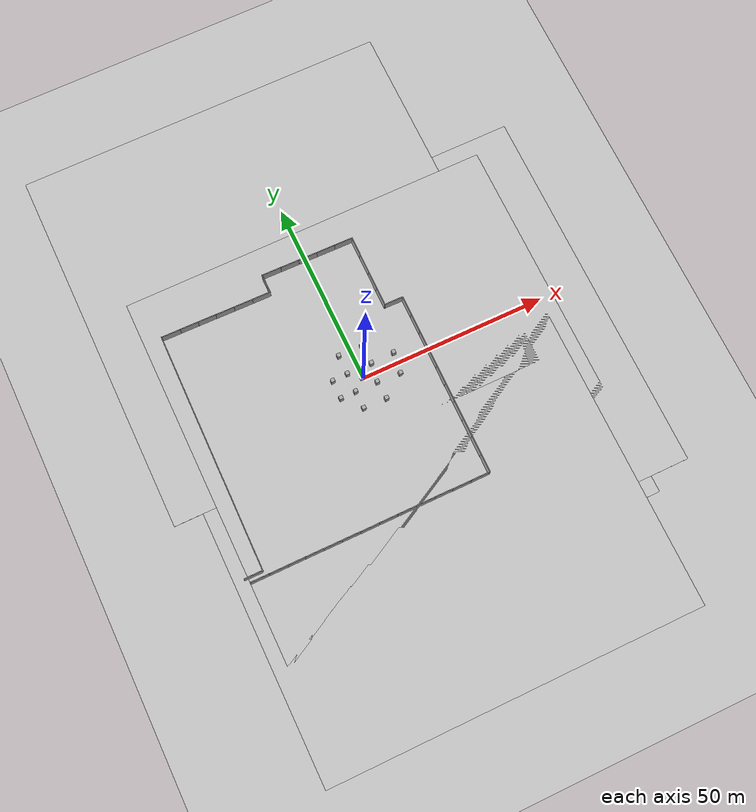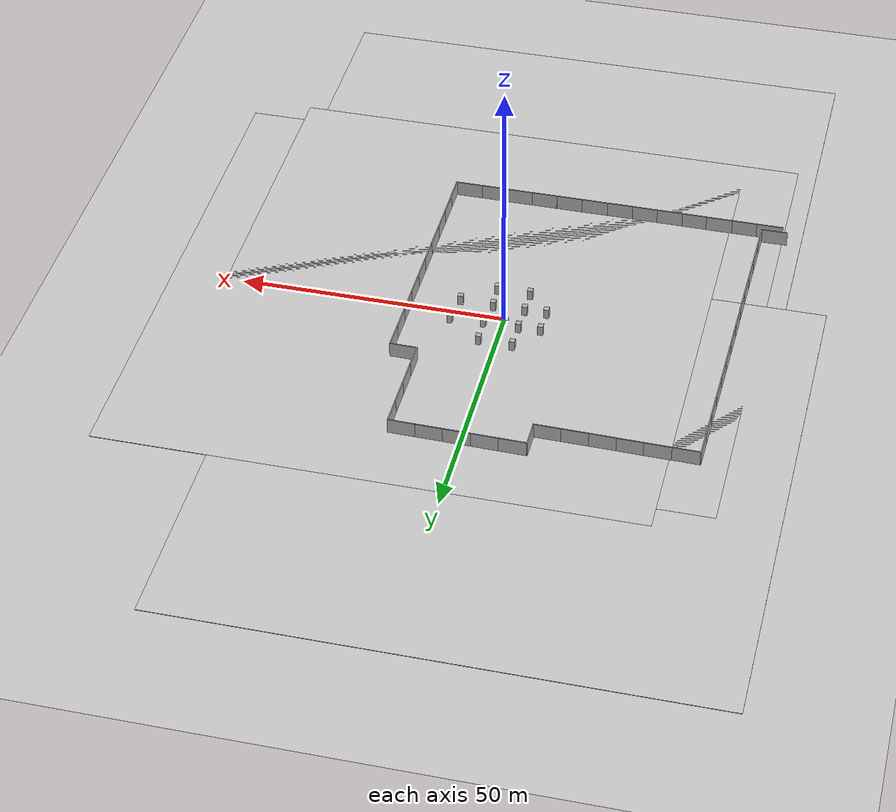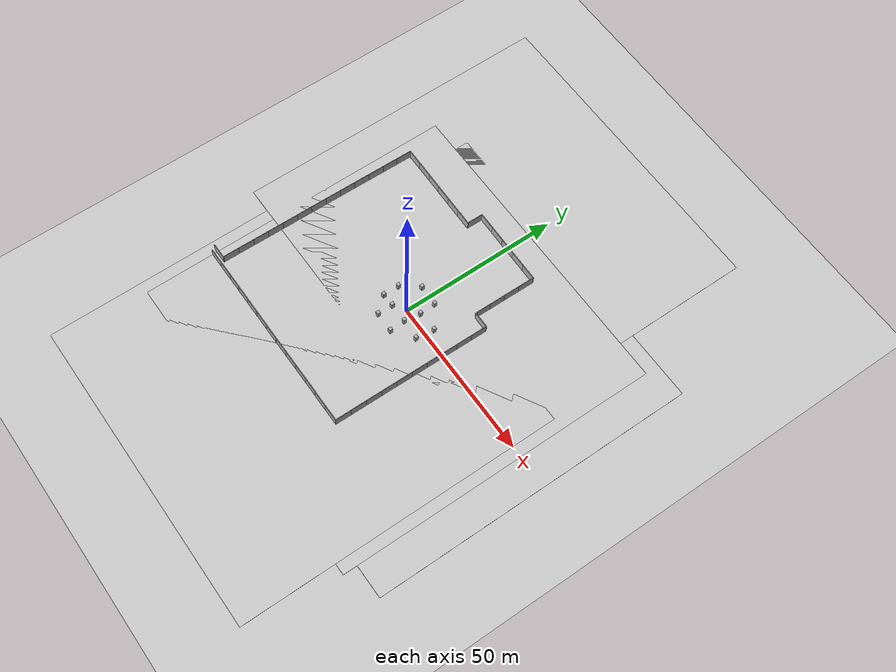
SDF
<sdf version='1.9'>
  <world name='block_room'>
    <physics name='1ms' type='ignored'>
      <max_step_size>0.001</max_step_size>
      <real_time_factor>1</real_time_factor>
      <real_time_update_rate>1000</real_time_update_rate>
    </physics>
    <plugin name='ignition::gazebo::systems::Physics' filename='libignition-gazebo-physics-system.so'/>
    <plugin name='ignition::gazebo::systems::UserCommands' filename='libignition-gazebo-user-commands-system.so'/>
    <plugin name='ignition::gazebo::systems::SceneBroadcaster' filename='libignition-gazebo-scene-broadcaster-system.so'/>
    <plugin name='ignition::gazebo::systems::Sensors' filename='libignition-gazebo-sensors-system.so'>
      <render_engine>ogre2</render_engine>
    </plugin>
    <gravity>0 0 -9.8</gravity>
    <magnetic_field>6e-06 2.3e-05 -4.2e-05</magnetic_field>
    <atmosphere type='adiabatic'/>
    <scene>
      <ambient>0.4 0.4 0.4 1</ambient>
      <background>0.7 0.7 0.7 1</background>
      <shadows>true</shadows>
    </scene>
    <model name='ground_plane'>
      <static>true</static>
      <link name='link'>
        <collision name='collision'>
          <geometry>
            <plane>
              <normal>0 0 1</normal>
              <size>100 100</size>
            </plane>
          </geometry>
          <surface>
            <friction>
              <ode>
                <mu>50</mu>
              </ode>
              <bullet>
                <friction>1</friction>
                <rolling_friction>0.10000000000000001</rolling_friction>
              </bullet>
            </friction>
            <bounce/>
            <contact/>
          </surface>
        </collision>
        <visual name='visual'>
          <geometry>
            <plane>
              <normal>0 0 1</normal>
              <size>100 100</size>
            </plane>
          </geometry>
          <material>
            <ambient>0.8 0.8 0.8 1</ambient>
            <diffuse>0.8 0.8 0.8 1</diffuse>
            <specular>0.8 0.8 0.8 1</specular>
          </material>
        </visual>
        <pose>0 0 0 0 -0 0</pose>
        <inertial>
          <pose>0 0 0 0 -0 0</pose>
          <mass>1</mass>
          <inertia>
            <ixx>1</ixx>
            <ixy>0</ixy>
            <ixz>0</ixz>
            <iyy>1</iyy>
            <iyz>0</iyz>
            <izz>1</izz>
          </inertia>
        </inertial>
        <enable_wind>false</enable_wind>
      </link>
      <pose>0 0 0 0 -0 0</pose>
      <self_collide>false</self_collide>
    </model>
    <include>
      <uri>file:///home/dliujm/um_files/rob_498_av/Autovehicle25/audi_ws/install/robot_desc/share/robot_desc/models/lucy</uri>
      <name>lucy_robot</name>
      <pose>-0 0 0 -0 0 -0</pose>
    </include>
    <model name='ground_plane_1'>
      <static>true</static>
      <link name='link'>
        <collision name='collision'>
          <geometry>
            <plane>
              <normal>0 0 1</normal>
              <size>100 100</size>
            </plane>
          </geometry>
          <surface>
            <friction>
              <ode>
                <mu>50</mu>
              </ode>
              <bullet>
                <friction>1</friction>
                <rolling_friction>0.10000000000000001</rolling_friction>
              </bullet>
            </friction>
            <bounce/>
            <contact/>
          </surface>
        </collision>
        <visual name='visual'>
          <geometry>
            <plane>
              <normal>0 0 1</normal>
              <size>100 100</size>
            </plane>
          </geometry>
          <material>
            <ambient>0.8 0.8 0.8 1</ambient>
            <diffuse>0.8 0.8 0.8 1</diffuse>
            <specular>0.8 0.8 0.8 1</specular>
          </material>
        </visual>
        <pose>0 0 0 0 -0 0</pose>
        <inertial>
          <pose>0 0 0 0 -0 0</pose>
          <mass>1</mass>
          <inertia>
            <ixx>1</ixx>
            <ixy>0</ixy>
            <ixz>0</ixz>
            <iyy>1</iyy>
            <iyz>0</iyz>
            <izz>1</izz>
          </inertia>
        </inertial>
        <enable_wind>false</enable_wind>
      </link>
      <pose>3.37132 -6.94607 0 0 -0 0</pose>
      <self_collide>false</self_collide>
    </model>
    <model name='ground_plane_1_1'>
      <static>true</static>
      <link name='link'>
        <collision name='collision'>
          <geometry>
            <plane>
              <normal>0 0 1</normal>
              <size>100 100</size>
            </plane>
          </geometry>
          <surface>
            <friction>
              <ode>
                <mu>50</mu>
              </ode>
              <bullet>
                <friction>1</friction>
                <rolling_friction>0.10000000000000001</rolling_friction>
              </bullet>
            </friction>
            <bounce/>
            <contact/>
          </surface>
        </collision>
        <visual name='visual'>
          <geometry>
            <plane>
              <normal>0 0 1</normal>
              <size>100 100</size>
            </plane>
          </geometry>
          <material>
            <ambient>0.8 0.8 0.8 1</ambient>
            <diffuse>0.8 0.8 0.8 1</diffuse>
            <specular>0.8 0.8 0.8 1</specular>
          </material>
        </visual>
        <pose>0 0 0 0 -0 0</pose>
        <inertial>
          <pose>0 0 0 0 -0 0</pose>
          <mass>1</mass>
          <inertia>
            <ixx>1</ixx>
            <ixy>0</ixy>
            <ixz>0</ixz>
            <iyy>1</iyy>
            <iyz>0</iyz>
            <izz>1</izz>
          </inertia>
        </inertial>
        <enable_wind>false</enable_wind>
      </link>
      <pose>13.6849 -2.64222 0 0 -0 0</pose>
      <self_collide>false</self_collide>
    </model>
    <model name='wall'>
      <static>true</static>
      <link name='link'>
        <collision name='collision'>
          <geometry>
            <box>
              <size>5 0.2 3</size>
            </box>
          </geometry>
          <surface>
            <friction>
              <ode/>
            </friction>
            <bounce/>
            <contact/>
          </surface>
        </collision>
        <visual name='visual'>
          <geometry>
            <box>
              <size>5 0.2 3</size>
            </box>
          </geometry>
          <material>
            <ambient>0.7 0.7 0.7 1</ambient>
            <diffuse>0.7 0.7 0.7 1</diffuse>
          </material>
        </visual>
        <pose>0 0 0 0 -0 0</pose>
        <inertial>
          <pose>0 0 0 0 -0 0</pose>
          <mass>1</mass>
          <inertia>
            <ixx>1</ixx>
            <ixy>0</ixy>
            <ixz>0</ixz>
            <iyy>1</iyy>
            <iyz>0</iyz>
            <izz>1</izz>
          </inertia>
        </inertial>
        <enable_wind>false</enable_wind>
      </link>
      <pose>0 -35.2766 1.50449 0 -0 0</pose>
      <self_collide>false</self_collide>
    </model>
    <model name='ground_plane_1_2'>
      <static>true</static>
      <link name='link'>
        <collision name='collision'>
          <geometry>
            <plane>
              <normal>0 0 1</normal>
              <size>100 100</size>
            </plane>
          </geometry>
          <surface>
            <friction>
              <ode>
                <mu>50</mu>
              </ode>
              <bullet>
                <friction>1</friction>
                <rolling_friction>0.10000000000000001</rolling_friction>
              </bullet>
            </friction>
            <bounce/>
            <contact/>
          </surface>
        </collision>
        <visual name='visual'>
          <geometry>
            <plane>
              <normal>0 0 1</normal>
              <size>100 100</size>
            </plane>
          </geometry>
          <material>
            <ambient>0.8 0.8 0.8 1</ambient>
            <diffuse>0.8 0.8 0.8 1</diffuse>
            <specular>0.8 0.8 0.8 1</specular>
          </material>
        </visual>
        <pose>0 0 0 0 -0 0</pose>
        <inertial>
          <pose>0 0 0 0 -0 0</pose>
          <mass>1</mass>
          <inertia>
            <ixx>1</ixx>
            <ixy>0</ixy>
            <ixz>0</ixz>
            <iyy>1</iyy>
            <iyz>0</iyz>
            <izz>1</izz>
          </inertia>
        </inertial>
        <enable_wind>false</enable_wind>
      </link>
      <pose>-0.202127 -35.9388 0 0 -0 0</pose>
      <self_collide>false</self_collide>
    </model>
    <model name='wall_1'>
      <static>true</static>
      <link name='link'>
        <collision name='collision'>
          <geometry>
            <box>
              <size>5 0.2 3</size>
            </box>
          </geometry>
          <surface>
            <friction>
              <ode/>
            </friction>
            <bounce/>
            <contact/>
          </surface>
        </collision>
        <visual name='visual'>
          <geometry>
            <box>
              <size>5 0.2 3</size>
            </box>
          </geometry>
          <material>
            <ambient>0.7 0.7 0.7 1</ambient>
            <diffuse>0.7 0.7 0.7 1</diffuse>
          </material>
        </visual>
        <pose>0 0 0 0 -0 0</pose>
        <inertial>
          <pose>0 0 0 0 -0 0</pose>
          <mass>1</mass>
          <inertia>
            <ixx>1</ixx>
            <ixy>0</ixy>
            <ixz>0</ixz>
            <iyy>1</iyy>
            <iyz>0</iyz>
            <izz>1</izz>
          </inertia>
        </inertial>
        <enable_wind>false</enable_wind>
      </link>
      <pose>-5.01711 -35.2867 1.50449 0 -0 0</pose>
      <self_collide>false</self_collide>
    </model>
    <model name='wall_2'>
      <static>true</static>
      <link name='link'>
        <collision name='collision'>
          <geometry>
            <box>
              <size>5 0.2 3</size>
            </box>
          </geometry>
          <surface>
            <friction>
              <ode/>
            </friction>
            <bounce/>
            <contact/>
          </surface>
        </collision>
        <visual name='visual'>
          <geometry>
            <box>
              <size>5 0.2 3</size>
            </box>
          </geometry>
          <material>
            <ambient>0.7 0.7 0.7 1</ambient>
            <diffuse>0.7 0.7 0.7 1</diffuse>
          </material>
        </visual>
        <pose>0 0 0 0 -0 0</pose>
        <inertial>
          <pose>0 0 0 0 -0 0</pose>
          <mass>1</mass>
          <inertia>
            <ixx>1</ixx>
            <ixy>0</ixy>
            <ixz>0</ixz>
            <iyy>1</iyy>
            <iyz>0</iyz>
            <izz>1</izz>
          </inertia>
        </inertial>
        <enable_wind>false</enable_wind>
      </link>
      <pose>-10.0087 -35.2904 1.50449 0 -0 0</pose>
      <self_collide>false</self_collide>
    </model>
    <model name='wall_3'>
      <static>true</static>
      <link name='link'>
        <collision name='collision'>
          <geometry>
            <box>
              <size>5 0.2 3</size>
            </box>
          </geometry>
          <surface>
            <friction>
              <ode/>
            </friction>
            <bounce/>
            <contact/>
          </surface>
        </collision>
        <visual name='visual'>
          <geometry>
            <box>
              <size>5 0.2 3</size>
            </box>
          </geometry>
          <material>
            <ambient>0.7 0.7 0.7 1</ambient>
            <diffuse>0.7 0.7 0.7 1</diffuse>
          </material>
        </visual>
        <pose>0 0 0 0 -0 0</pose>
        <inertial>
          <pose>0 0 0 0 -0 0</pose>
          <mass>1</mass>
          <inertia>
            <ixx>1</ixx>
            <ixy>0</ixy>
            <ixz>0</ixz>
            <iyy>1</iyy>
            <iyz>0</iyz>
            <izz>1</izz>
          </inertia>
        </inertial>
        <enable_wind>false</enable_wind>
      </link>
      <pose>4.87545 -35.2716 1.50449 0 -0 0</pose>
      <self_collide>false</self_collide>
    </model>
    <model name='wall_4'>
      <static>true</static>
      <link name='link'>
        <collision name='collision'>
          <geometry>
            <box>
              <size>5 0.2 3</size>
            </box>
          </geometry>
          <surface>
            <friction>
              <ode/>
            </friction>
            <bounce/>
            <contact/>
          </surface>
        </collision>
        <visual name='visual'>
          <geometry>
            <box>
              <size>5 0.2 3</size>
            </box>
          </geometry>
          <material>
            <ambient>0.7 0.7 0.7 1</ambient>
            <diffuse>0.7 0.7 0.7 1</diffuse>
          </material>
        </visual>
        <pose>0 0 0 0 -0 0</pose>
        <inertial>
          <pose>0 0 0 0 -0 0</pose>
          <mass>1</mass>
          <inertia>
            <ixx>1</ixx>
            <ixy>0</ixy>
            <ixz>0</ixz>
            <iyy>1</iyy>
            <iyz>0</iyz>
            <izz>1</izz>
          </inertia>
        </inertial>
        <enable_wind>false</enable_wind>
      </link>
      <pose>9.82758 -35.33 1.50449 0 -0 0</pose>
      <self_collide>false</self_collide>
    </model>
    <model name='wall_5'>
      <static>true</static>
      <link name='link'>
        <collision name='collision'>
          <geometry>
            <box>
              <size>5 0.2 3</size>
            </box>
          </geometry>
          <surface>
            <friction>
              <ode/>
            </friction>
            <bounce/>
            <contact/>
          </surface>
        </collision>
        <visual name='visual'>
          <geometry>
            <box>
              <size>5 0.2 3</size>
            </box>
          </geometry>
          <material>
            <ambient>0.7 0.7 0.7 1</ambient>
            <diffuse>0.7 0.7 0.7 1</diffuse>
          </material>
        </visual>
        <pose>0 0 0 0 -0 0</pose>
        <inertial>
          <pose>0 0 0 0 -0 0</pose>
          <mass>1</mass>
          <inertia>
            <ixx>1</ixx>
            <ixy>0</ixy>
            <ixz>0</ixz>
            <iyy>1</iyy>
            <iyz>0</iyz>
            <izz>1</izz>
          </inertia>
        </inertial>
        <enable_wind>false</enable_wind>
      </link>
      <pose>14.8056 -35.3183 1.50449 0 -0 0</pose>
      <self_collide>false</self_collide>
    </model>
    <model name='wall_7'>
      <static>true</static>
      <link name='link'>
        <collision name='collision'>
          <geometry>
            <box>
              <size>5 0.2 3</size>
            </box>
          </geometry>
          <surface>
            <friction>
              <ode/>
            </friction>
            <bounce/>
            <contact/>
          </surface>
        </collision>
        <visual name='visual'>
          <geometry>
            <box>
              <size>5 0.2 3</size>
            </box>
          </geometry>
          <material>
            <ambient>0.7 0.7 0.7 1</ambient>
            <diffuse>0.7 0.7 0.7 1</diffuse>
          </material>
        </visual>
        <pose>0 0 0 0 -0 0</pose>
        <inertial>
          <pose>0 0 0 0 -0 0</pose>
          <mass>1</mass>
          <inertia>
            <ixx>1</ixx>
            <ixy>0</ixy>
            <ixz>0</ixz>
            <iyy>1</iyy>
            <iyz>0</iyz>
            <izz>1</izz>
          </inertia>
        </inertial>
        <enable_wind>false</enable_wind>
      </link>
      <pose>17.4193 -32.9231 1.50449 0 0 -1.57867</pose>
      <self_collide>false</self_collide>
    </model>
    <model name='wall_7_1'>
      <static>true</static>
      <link name='link'>
        <collision name='collision'>
          <geometry>
            <box>
              <size>5 0.2 3</size>
            </box>
          </geometry>
          <surface>
            <friction>
              <ode/>
            </friction>
            <bounce/>
            <contact/>
          </surface>
        </collision>
        <visual name='visual'>
          <geometry>
            <box>
              <size>5 0.2 3</size>
            </box>
          </geometry>
          <material>
            <ambient>0.7 0.7 0.7 1</ambient>
            <diffuse>0.7 0.7 0.7 1</diffuse>
          </material>
        </visual>
        <pose>0 0 0 0 -0 0</pose>
        <inertial>
          <pose>0 0 0 0 -0 0</pose>
          <mass>1</mass>
          <inertia>
            <ixx>1</ixx>
            <ixy>0</ixy>
            <ixz>0</ixz>
            <iyy>1</iyy>
            <iyz>0</iyz>
            <izz>1</izz>
          </inertia>
        </inertial>
        <enable_wind>false</enable_wind>
      </link>
      <pose>17.4426 -27.9423 1.50449 0 0 -1.57867</pose>
      <self_collide>false</self_collide>
    </model>
    <model name='wall_7_2'>
      <static>true</static>
      <link name='link'>
        <collision name='collision'>
          <geometry>
            <box>
              <size>5 0.2 3</size>
            </box>
          </geometry>
          <surface>
            <friction>
              <ode/>
            </friction>
            <bounce/>
            <contact/>
          </surface>
        </collision>
        <visual name='visual'>
          <geometry>
            <box>
              <size>5 0.2 3</size>
            </box>
          </geometry>
          <material>
            <ambient>0.7 0.7 0.7 1</ambient>
            <diffuse>0.7 0.7 0.7 1</diffuse>
          </material>
        </visual>
        <pose>0 0 0 0 -0 0</pose>
        <inertial>
          <pose>0 0 0 0 -0 0</pose>
          <mass>1</mass>
          <inertia>
            <ixx>1</ixx>
            <ixy>0</ixy>
            <ixz>0</ixz>
            <iyy>1</iyy>
            <iyz>0</iyz>
            <izz>1</izz>
          </inertia>
        </inertial>
        <enable_wind>false</enable_wind>
      </link>
      <pose>17.4693 -22.9812 1.50449 0 0 -1.57867</pose>
      <self_collide>false</self_collide>
    </model>
    <model name='wall_7_3'>
      <static>true</static>
      <link name='link'>
        <collision name='collision'>
          <geometry>
            <box>
              <size>5 0.2 3</size>
            </box>
          </geometry>
          <surface>
            <friction>
              <ode/>
            </friction>
            <bounce/>
            <contact/>
          </surface>
        </collision>
        <visual name='visual'>
          <geometry>
            <box>
              <size>5 0.2 3</size>
            </box>
          </geometry>
          <material>
            <ambient>0.7 0.7 0.7 1</ambient>
            <diffuse>0.7 0.7 0.7 1</diffuse>
          </material>
        </visual>
        <pose>0 0 0 0 -0 0</pose>
        <inertial>
          <pose>0 0 0 0 -0 0</pose>
          <mass>1</mass>
          <inertia>
            <ixx>1</ixx>
            <ixy>0</ixy>
            <ixz>0</ixz>
            <iyy>1</iyy>
            <iyz>0</iyz>
            <izz>1</izz>
          </inertia>
        </inertial>
        <enable_wind>false</enable_wind>
      </link>
      <pose>17.508 -18.0005 1.50449 0 0 -1.57867</pose>
      <self_collide>false</self_collide>
    </model>
    <model name='wall_7_4'>
      <static>true</static>
      <link name='link'>
        <collision name='collision'>
          <geometry>
            <box>
              <size>5 0.2 3</size>
            </box>
          </geometry>
          <surface>
            <friction>
              <ode/>
            </friction>
            <bounce/>
            <contact/>
          </surface>
        </collision>
        <visual name='visual'>
          <geometry>
            <box>
              <size>5 0.2 3</size>
            </box>
          </geometry>
          <material>
            <ambient>0.7 0.7 0.7 1</ambient>
            <diffuse>0.7 0.7 0.7 1</diffuse>
          </material>
        </visual>
        <pose>0 0 0 0 -0 0</pose>
        <inertial>
          <pose>0 0 0 0 -0 0</pose>
          <mass>1</mass>
          <inertia>
            <ixx>1</ixx>
            <ixy>0</ixy>
            <ixz>0</ixz>
            <iyy>1</iyy>
            <iyz>0</iyz>
            <izz>1</izz>
          </inertia>
        </inertial>
        <enable_wind>false</enable_wind>
      </link>
      <pose>17.5521 -12.9986 1.50449 0 0 -1.57867</pose>
      <self_collide>false</self_collide>
    </model>
    <model name='wall_7_5'>
      <static>true</static>
      <link name='link'>
        <collision name='collision'>
          <geometry>
            <box>
              <size>5 0.2 3</size>
            </box>
          </geometry>
          <surface>
            <friction>
              <ode/>
            </friction>
            <bounce/>
            <contact/>
          </surface>
        </collision>
        <visual name='visual'>
          <geometry>
            <box>
              <size>5 0.2 3</size>
            </box>
          </geometry>
          <material>
            <ambient>0.7 0.7 0.7 1</ambient>
            <diffuse>0.7 0.7 0.7 1</diffuse>
          </material>
        </visual>
        <pose>0 0 0 0 -0 0</pose>
        <inertial>
          <pose>0 0 0 0 -0 0</pose>
          <mass>1</mass>
          <inertia>
            <ixx>1</ixx>
            <ixy>0</ixy>
            <ixz>0</ixz>
            <iyy>1</iyy>
            <iyz>0</iyz>
            <izz>1</izz>
          </inertia>
        </inertial>
        <enable_wind>false</enable_wind>
      </link>
      <pose>17.5839 -7.99492 1.50449 0 0 -1.57867</pose>
      <self_collide>false</self_collide>
    </model>
    <model name='wall_7_6'>
      <static>true</static>
      <link name='link'>
        <collision name='collision'>
          <geometry>
            <box>
              <size>5 0.2 3</size>
            </box>
          </geometry>
          <surface>
            <friction>
              <ode/>
            </friction>
            <bounce/>
            <contact/>
          </surface>
        </collision>
        <visual name='visual'>
          <geometry>
            <box>
              <size>5 0.2 3</size>
            </box>
          </geometry>
          <material>
            <ambient>0.7 0.7 0.7 1</ambient>
            <diffuse>0.7 0.7 0.7 1</diffuse>
          </material>
        </visual>
        <pose>0 0 0 0 -0 0</pose>
        <inertial>
          <pose>0 0 0 0 -0 0</pose>
          <mass>1</mass>
          <inertia>
            <ixx>1</ixx>
            <ixy>0</ixy>
            <ixz>0</ixz>
            <iyy>1</iyy>
            <iyz>0</iyz>
            <izz>1</izz>
          </inertia>
        </inertial>
        <enable_wind>false</enable_wind>
      </link>
      <pose>17.6254 -3.00807 1.50449 0 0 -1.57867</pose>
      <self_collide>false</self_collide>
    </model>
    <model name='wall_7_7'>
      <static>true</static>
      <link name='link'>
        <collision name='collision'>
          <geometry>
            <box>
              <size>5 0.2 3</size>
            </box>
          </geometry>
          <surface>
            <friction>
              <ode/>
            </friction>
            <bounce/>
            <contact/>
          </surface>
        </collision>
        <visual name='visual'>
          <geometry>
            <box>
              <size>5 0.2 3</size>
            </box>
          </geometry>
          <material>
            <ambient>0.7 0.7 0.7 1</ambient>
            <diffuse>0.7 0.7 0.7 1</diffuse>
          </material>
        </visual>
        <pose>0 0 0 0 -0 0</pose>
        <inertial>
          <pose>0 0 0 0 -0 0</pose>
          <mass>1</mass>
          <inertia>
            <ixx>1</ixx>
            <ixy>0</ixy>
            <ixz>0</ixz>
            <iyy>1</iyy>
            <iyz>0</iyz>
            <izz>1</izz>
          </inertia>
        </inertial>
        <enable_wind>false</enable_wind>
      </link>
      <pose>17.6643 1.98188 1.50449 0 0 -1.57867</pose>
      <self_collide>false</self_collide>
    </model>
    <model name='wall_7_8'>
      <static>true</static>
      <link name='link'>
        <collision name='collision'>
          <geometry>
            <box>
              <size>5 0.2 3</size>
            </box>
          </geometry>
          <surface>
            <friction>
              <ode/>
            </friction>
            <bounce/>
            <contact/>
          </surface>
        </collision>
        <visual name='visual'>
          <geometry>
            <box>
              <size>5 0.2 3</size>
            </box>
          </geometry>
          <material>
            <ambient>0.7 0.7 0.7 1</ambient>
            <diffuse>0.7 0.7 0.7 1</diffuse>
          </material>
        </visual>
        <pose>0 0 0 0 -0 0</pose>
        <inertial>
          <pose>0 0 0 0 -0 0</pose>
          <mass>1</mass>
          <inertia>
            <ixx>1</ixx>
            <ixy>0</ixy>
            <ixz>0</ixz>
            <iyy>1</iyy>
            <iyz>0</iyz>
            <izz>1</izz>
          </inertia>
        </inertial>
        <enable_wind>false</enable_wind>
      </link>
      <pose>17.7003 6.98697 1.50449 0 0 -1.57867</pose>
      <self_collide>false</self_collide>
    </model>
    <model name='wall_7_9'>
      <static>true</static>
      <link name='link'>
        <collision name='collision'>
          <geometry>
            <box>
              <size>5 0.2 3</size>
            </box>
          </geometry>
          <surface>
            <friction>
              <ode/>
            </friction>
            <bounce/>
            <contact/>
          </surface>
        </collision>
        <visual name='visual'>
          <geometry>
            <box>
              <size>5 0.2 3</size>
            </box>
          </geometry>
          <material>
            <ambient>0.7 0.7 0.7 1</ambient>
            <diffuse>0.7 0.7 0.7 1</diffuse>
          </material>
        </visual>
        <pose>0 0 0 0 -0 0</pose>
        <inertial>
          <pose>0 0 0 0 -0 0</pose>
          <mass>1</mass>
          <inertia>
            <ixx>1</ixx>
            <ixy>0</ixy>
            <ixz>0</ixz>
            <iyy>1</iyy>
            <iyz>0</iyz>
            <izz>1</izz>
          </inertia>
        </inertial>
        <enable_wind>false</enable_wind>
      </link>
      <pose>17.744 11.9433 1.50449 0 0 -1.57867</pose>
      <self_collide>false</self_collide>
    </model>
    <model name='wall_7_10'>
      <static>true</static>
      <link name='link'>
        <collision name='collision'>
          <geometry>
            <box>
              <size>5 0.2 3</size>
            </box>
          </geometry>
          <surface>
            <friction>
              <ode/>
            </friction>
            <bounce/>
            <contact/>
          </surface>
        </collision>
        <visual name='visual'>
          <geometry>
            <box>
              <size>5 0.2 3</size>
            </box>
          </geometry>
          <material>
            <ambient>0.7 0.7 0.7 1</ambient>
            <diffuse>0.7 0.7 0.7 1</diffuse>
          </material>
        </visual>
        <pose>0 0 0 0 -0 0</pose>
        <inertial>
          <pose>0 0 0 0 -0 0</pose>
          <mass>1</mass>
          <inertia>
            <ixx>1</ixx>
            <ixy>0</ixy>
            <ixz>0</ixz>
            <iyy>1</iyy>
            <iyz>0</iyz>
            <izz>1</izz>
          </inertia>
        </inertial>
        <enable_wind>false</enable_wind>
      </link>
      <pose>15.3706 14.5675 1.50449 0 -0 3.12423</pose>
      <self_collide>false</self_collide>
    </model>
    <model name='wall_7_9_1'>
      <static>true</static>
      <link name='link'>
        <collision name='collision'>
          <geometry>
            <box>
              <size>5 0.2 3</size>
            </box>
          </geometry>
          <surface>
            <friction>
              <ode/>
            </friction>
            <bounce/>
            <contact/>
          </surface>
        </collision>
        <visual name='visual'>
          <geometry>
            <box>
              <size>5 0.2 3</size>
            </box>
          </geometry>
          <material>
            <ambient>0.7 0.7 0.7 1</ambient>
            <diffuse>0.7 0.7 0.7 1</diffuse>
          </material>
        </visual>
        <pose>0 0 0 0 -0 0</pose>
        <inertial>
          <pose>0 0 0 0 -0 0</pose>
          <mass>1</mass>
          <inertia>
            <ixx>1</ixx>
            <ixy>0</ixy>
            <ixz>0</ixz>
            <iyy>1</iyy>
            <iyz>0</iyz>
            <izz>1</izz>
          </inertia>
        </inertial>
        <enable_wind>false</enable_wind>
      </link>
      <pose>12.7866 17.0253 1.50449 0 0 -1.57867</pose>
      <self_collide>false</self_collide>
    </model>
    <model name='wall_7_9_2'>
      <static>true</static>
      <link name='link'>
        <collision name='collision'>
          <geometry>
            <box>
              <size>5 0.2 3</size>
            </box>
          </geometry>
          <surface>
            <friction>
              <ode/>
            </friction>
            <bounce/>
            <contact/>
          </surface>
        </collision>
        <visual name='visual'>
          <geometry>
            <box>
              <size>5 0.2 3</size>
            </box>
          </geometry>
          <material>
            <ambient>0.7 0.7 0.7 1</ambient>
            <diffuse>0.7 0.7 0.7 1</diffuse>
          </material>
        </visual>
        <pose>0 0 0 0 -0 0</pose>
        <inertial>
          <pose>0 0 0 0 -0 0</pose>
          <mass>1</mass>
          <inertia>
            <ixx>1</ixx>
            <ixy>0</ixy>
            <ixz>0</ixz>
            <iyy>1</iyy>
            <iyz>0</iyz>
            <izz>1</izz>
          </inertia>
        </inertial>
        <enable_wind>false</enable_wind>
      </link>
      <pose>12.8326 21.9834 1.50449 0 0 -1.57867</pose>
      <self_collide>false</self_collide>
    </model>
    <model name='wall_7_9_3'>
      <static>true</static>
      <link name='link'>
        <collision name='collision'>
          <geometry>
            <box>
              <size>5 0.2 3</size>
            </box>
          </geometry>
          <surface>
            <friction>
              <ode/>
            </friction>
            <bounce/>
            <contact/>
          </surface>
        </collision>
        <visual name='visual'>
          <geometry>
            <box>
              <size>5 0.2 3</size>
            </box>
          </geometry>
          <material>
            <ambient>0.7 0.7 0.7 1</ambient>
            <diffuse>0.7 0.7 0.7 1</diffuse>
          </material>
        </visual>
        <pose>0 0 0 0 -0 0</pose>
        <inertial>
          <pose>0 0 0 0 -0 0</pose>
          <mass>1</mass>
          <inertia>
            <ixx>1</ixx>
            <ixy>0</ixy>
            <ixz>0</ixz>
            <iyy>1</iyy>
            <iyz>0</iyz>
            <izz>1</izz>
          </inertia>
        </inertial>
        <enable_wind>false</enable_wind>
      </link>
      <pose>12.8732 26.9224 1.50449 0 0 -1.57867</pose>
      <self_collide>false</self_collide>
    </model>
    <model name='wall_7_9_4'>
      <static>true</static>
      <link name='link'>
        <collision name='collision'>
          <geometry>
            <box>
              <size>5 0.2 3</size>
            </box>
          </geometry>
          <surface>
            <friction>
              <ode/>
            </friction>
            <bounce/>
            <contact/>
          </surface>
        </collision>
        <visual name='visual'>
          <geometry>
            <box>
              <size>5 0.2 3</size>
            </box>
          </geometry>
          <material>
            <ambient>0.7 0.7 0.7 1</ambient>
            <diffuse>0.7 0.7 0.7 1</diffuse>
          </material>
        </visual>
        <pose>0 0 0 0 -0 0</pose>
        <inertial>
          <pose>0 0 0 0 -0 0</pose>
          <mass>1</mass>
          <inertia>
            <ixx>1</ixx>
            <ixy>0</ixy>
            <ixz>0</ixz>
            <iyy>1</iyy>
            <iyz>0</iyz>
            <izz>1</izz>
          </inertia>
        </inertial>
        <enable_wind>false</enable_wind>
      </link>
      <pose>12.917 31.9173 1.50449 0 0 -1.57867</pose>
      <self_collide>false</self_collide>
    </model>
    <model name='wall_7_10_1'>
      <static>true</static>
      <link name='link'>
        <collision name='collision'>
          <geometry>
            <box>
              <size>5 0.2 3</size>
            </box>
          </geometry>
          <surface>
            <friction>
              <ode/>
            </friction>
            <bounce/>
            <contact/>
          </surface>
        </collision>
        <visual name='visual'>
          <geometry>
            <box>
              <size>5 0.2 3</size>
            </box>
          </geometry>
          <material>
            <ambient>0.7 0.7 0.7 1</ambient>
            <diffuse>0.7 0.7 0.7 1</diffuse>
          </material>
        </visual>
        <pose>0 0 0 0 -0 0</pose>
        <inertial>
          <pose>0 0 0 0 -0 0</pose>
          <mass>1</mass>
          <inertia>
            <ixx>1</ixx>
            <ixy>0</ixy>
            <ixz>0</ixz>
            <iyy>1</iyy>
            <iyz>0</iyz>
            <izz>1</izz>
          </inertia>
        </inertial>
        <enable_wind>false</enable_wind>
      </link>
      <pose>10.5507 34.5647 1.50449 0 -0 3.12423</pose>
      <self_collide>false</self_collide>
    </model>
    <model name='wall_7_10_2'>
      <static>true</static>
      <link name='link'>
        <collision name='collision'>
          <geometry>
            <box>
              <size>5 0.2 3</size>
            </box>
          </geometry>
          <surface>
            <friction>
              <ode/>
            </friction>
            <bounce/>
            <contact/>
          </surface>
        </collision>
        <visual name='visual'>
          <geometry>
            <box>
              <size>5 0.2 3</size>
            </box>
          </geometry>
          <material>
            <ambient>0.7 0.7 0.7 1</ambient>
            <diffuse>0.7 0.7 0.7 1</diffuse>
          </material>
        </visual>
        <pose>0 0 0 0 -0 0</pose>
        <inertial>
          <pose>0 0 0 0 -0 0</pose>
          <mass>1</mass>
          <inertia>
            <ixx>1</ixx>
            <ixy>0</ixy>
            <ixz>0</ixz>
            <iyy>1</iyy>
            <iyz>0</iyz>
            <izz>1</izz>
          </inertia>
        </inertial>
        <enable_wind>false</enable_wind>
      </link>
      <pose>5.54363 34.6488 1.50449 0 -0 3.12423</pose>
      <self_collide>false</self_collide>
    </model>
    <model name='wall_7_10_3'>
      <static>true</static>
      <link name='link'>
        <collision name='collision'>
          <geometry>
            <box>
              <size>5 0.2 3</size>
            </box>
          </geometry>
          <surface>
            <friction>
              <ode/>
            </friction>
            <bounce/>
            <contact/>
          </surface>
        </collision>
        <visual name='visual'>
          <geometry>
            <box>
              <size>5 0.2 3</size>
            </box>
          </geometry>
          <material>
            <ambient>0.7 0.7 0.7 1</ambient>
            <diffuse>0.7 0.7 0.7 1</diffuse>
          </material>
        </visual>
        <pose>0 0 0 0 -0 0</pose>
        <inertial>
          <pose>0 0 0 0 -0 0</pose>
          <mass>1</mass>
          <inertia>
            <ixx>1</ixx>
            <ixy>0</ixy>
            <ixz>0</ixz>
            <iyy>1</iyy>
            <iyz>0</iyz>
            <izz>1</izz>
          </inertia>
        </inertial>
        <enable_wind>false</enable_wind>
      </link>
      <pose>0.571802 34.7384 1.50449 0 -0 3.12423</pose>
      <self_collide>false</self_collide>
    </model>
    <model name='wall_7_10_4'>
      <static>true</static>
      <link name='link'>
        <collision name='collision'>
          <geometry>
            <box>
              <size>5 0.2 3</size>
            </box>
          </geometry>
          <surface>
            <friction>
              <ode/>
            </friction>
            <bounce/>
            <contact/>
          </surface>
        </collision>
        <visual name='visual'>
          <geometry>
            <box>
              <size>5 0.2 3</size>
            </box>
          </geometry>
          <material>
            <ambient>0.7 0.7 0.7 1</ambient>
            <diffuse>0.7 0.7 0.7 1</diffuse>
          </material>
        </visual>
        <pose>0 0 0 0 -0 0</pose>
        <inertial>
          <pose>0 0 0 0 -0 0</pose>
          <mass>1</mass>
          <inertia>
            <ixx>1</ixx>
            <ixy>0</ixy>
            <ixz>0</ixz>
            <iyy>1</iyy>
            <iyz>0</iyz>
            <izz>1</izz>
          </inertia>
        </inertial>
        <enable_wind>false</enable_wind>
      </link>
      <pose>-4.45933 34.8251 1.50449 0 -0 3.12423</pose>
      <self_collide>false</self_collide>
    </model>
    <model name='wall_7_10_5'>
      <static>true</static>
      <link name='link'>
        <collision name='collision'>
          <geometry>
            <box>
              <size>5 0.2 3</size>
            </box>
          </geometry>
          <surface>
            <friction>
              <ode/>
            </friction>
            <bounce/>
            <contact/>
          </surface>
        </collision>
        <visual name='visual'>
          <geometry>
            <box>
              <size>5 0.2 3</size>
            </box>
          </geometry>
          <material>
            <ambient>0.7 0.7 0.7 1</ambient>
            <diffuse>0.7 0.7 0.7 1</diffuse>
          </material>
        </visual>
        <pose>0 0 0 0 -0 0</pose>
        <inertial>
          <pose>0 0 0 0 -0 0</pose>
          <mass>1</mass>
          <inertia>
            <ixx>1</ixx>
            <ixy>0</ixy>
            <ixz>0</ixz>
            <iyy>1</iyy>
            <iyz>0</iyz>
            <izz>1</izz>
          </inertia>
        </inertial>
        <enable_wind>false</enable_wind>
      </link>
      <pose>-9.48187 34.9196 1.50449 0 -0 3.12423</pose>
      <self_collide>false</self_collide>
    </model>
    <model name='wall_7_10_5_1'>
      <static>true</static>
      <link name='link'>
        <collision name='collision'>
          <geometry>
            <box>
              <size>5 0.2 3</size>
            </box>
          </geometry>
          <surface>
            <friction>
              <ode/>
            </friction>
            <bounce/>
            <contact/>
          </surface>
        </collision>
        <visual name='visual'>
          <geometry>
            <box>
              <size>5 0.2 3</size>
            </box>
          </geometry>
          <material>
            <ambient>0.7 0.7 0.7 1</ambient>
            <diffuse>0.7 0.7 0.7 1</diffuse>
          </material>
        </visual>
        <pose>0 0 0 0 -0 0</pose>
        <inertial>
          <pose>0 0 0 0 -0 0</pose>
          <mass>1</mass>
          <inertia>
            <ixx>1</ixx>
            <ixy>0</ixy>
            <ixz>0</ixz>
            <iyy>1</iyy>
            <iyz>0</iyz>
            <izz>1</izz>
          </inertia>
        </inertial>
        <enable_wind>false</enable_wind>
      </link>
      <pose>-12.1066 32.5743 1.50449 0 0 -1.58082</pose>
      <self_collide>false</self_collide>
    </model>
    <model name='ground_plane_1_1_1'>
      <static>true</static>
      <link name='link'>
        <collision name='collision'>
          <geometry>
            <plane>
              <normal>0 0 1</normal>
              <size>100 100</size>
            </plane>
          </geometry>
          <surface>
            <friction>
              <ode>
                <mu>50</mu>
              </ode>
              <bullet>
                <friction>1</friction>
                <rolling_friction>0.10000000000000001</rolling_friction>
              </bullet>
            </friction>
            <bounce/>
            <contact/>
          </surface>
        </collision>
        <visual name='visual'>
          <geometry>
            <plane>
              <normal>0 0 1</normal>
              <size>100 100</size>
            </plane>
          </geometry>
          <material>
            <ambient>0.8 0.8 0.8 1</ambient>
            <diffuse>0.8 0.8 0.8 1</diffuse>
            <specular>0.8 0.8 0.8 1</specular>
          </material>
        </visual>
        <pose>0 0 0 0 -0 0</pose>
        <inertial>
          <pose>0 0 0 0 -0 0</pose>
          <mass>1</mass>
          <inertia>
            <ixx>1</ixx>
            <ixy>0</ixy>
            <ixz>0</ixz>
            <iyy>1</iyy>
            <iyz>0</iyz>
            <izz>1</izz>
          </inertia>
        </inertial>
        <enable_wind>false</enable_wind>
      </link>
      <pose>-7.7862 35.4267 0 0 -0 0</pose>
      <self_collide>false</self_collide>
    </model>
    <model name='wall_7_10_5_2'>
      <static>true</static>
      <link name='link'>
        <collision name='collision'>
          <geometry>
            <box>
              <size>5 0.2 3</size>
            </box>
          </geometry>
          <surface>
            <friction>
              <ode/>
            </friction>
            <bounce/>
            <contact/>
          </surface>
        </collision>
        <visual name='visual'>
          <geometry>
            <box>
              <size>5 0.2 3</size>
            </box>
          </geometry>
          <material>
            <ambient>0.7 0.7 0.7 1</ambient>
            <diffuse>0.7 0.7 0.7 1</diffuse>
          </material>
        </visual>
        <pose>0 0 0 0 -0 0</pose>
        <inertial>
          <pose>0 0 0 0 -0 0</pose>
          <mass>1</mass>
          <inertia>
            <ixx>1</ixx>
            <ixy>0</ixy>
            <ixz>0</ixz>
            <iyy>1</iyy>
            <iyz>0</iyz>
            <izz>1</izz>
          </inertia>
        </inertial>
        <enable_wind>false</enable_wind>
      </link>
      <pose>-14.5273 30.0144 1.50449 0 -0 3.12423</pose>
      <self_collide>false</self_collide>
    </model>
    <model name='wall_7_10_5_2_1'>
      <static>true</static>
      <link name='link'>
        <collision name='collision'>
          <geometry>
            <box>
              <size>5 0.2 3</size>
            </box>
          </geometry>
          <surface>
            <friction>
              <ode/>
            </friction>
            <bounce/>
            <contact/>
          </surface>
        </collision>
        <visual name='visual'>
          <geometry>
            <box>
              <size>5 0.2 3</size>
            </box>
          </geometry>
          <material>
            <ambient>0.7 0.7 0.7 1</ambient>
            <diffuse>0.7 0.7 0.7 1</diffuse>
          </material>
        </visual>
        <pose>0 0 0 0 -0 0</pose>
        <inertial>
          <pose>0 0 0 0 -0 0</pose>
          <mass>1</mass>
          <inertia>
            <ixx>1</ixx>
            <ixy>0</ixy>
            <ixz>0</ixz>
            <iyy>1</iyy>
            <iyz>0</iyz>
            <izz>1</izz>
          </inertia>
        </inertial>
        <enable_wind>false</enable_wind>
      </link>
      <pose>-19.5274 30.0957 1.50449 0 -0 3.12423</pose>
      <self_collide>false</self_collide>
    </model>
    <model name='wall_7_10_5_2_1_1'>
      <static>true</static>
      <link name='link'>
        <collision name='collision'>
          <geometry>
            <box>
              <size>5 0.2 3</size>
            </box>
          </geometry>
          <surface>
            <friction>
              <ode/>
            </friction>
            <bounce/>
            <contact/>
          </surface>
        </collision>
        <visual name='visual'>
          <geometry>
            <box>
              <size>5 0.2 3</size>
            </box>
          </geometry>
          <material>
            <ambient>0.7 0.7 0.7 1</ambient>
            <diffuse>0.7 0.7 0.7 1</diffuse>
          </material>
        </visual>
        <pose>0 0 0 0 -0 0</pose>
        <inertial>
          <pose>0 0 0 0 -0 0</pose>
          <mass>1</mass>
          <inertia>
            <ixx>1</ixx>
            <ixy>0</ixy>
            <ixz>0</ixz>
            <iyy>1</iyy>
            <iyz>0</iyz>
            <izz>1</izz>
          </inertia>
        </inertial>
        <enable_wind>false</enable_wind>
      </link>
      <pose>-24.5301 30.1772 1.50449 0 -0 3.12423</pose>
      <self_collide>false</self_collide>
    </model>
    <model name='wall_7_10_5_2_1_2'>
      <static>true</static>
      <link name='link'>
        <collision name='collision'>
          <geometry>
            <box>
              <size>5 0.2 3</size>
            </box>
          </geometry>
          <surface>
            <friction>
              <ode/>
            </friction>
            <bounce/>
            <contact/>
          </surface>
        </collision>
        <visual name='visual'>
          <geometry>
            <box>
              <size>5 0.2 3</size>
            </box>
          </geometry>
          <material>
            <ambient>0.7 0.7 0.7 1</ambient>
            <diffuse>0.7 0.7 0.7 1</diffuse>
          </material>
        </visual>
        <pose>0 0 0 0 -0 0</pose>
        <inertial>
          <pose>0 0 0 0 -0 0</pose>
          <mass>1</mass>
          <inertia>
            <ixx>1</ixx>
            <ixy>0</ixy>
            <ixz>0</ixz>
            <iyy>1</iyy>
            <iyz>0</iyz>
            <izz>1</izz>
          </inertia>
        </inertial>
        <enable_wind>false</enable_wind>
      </link>
      <pose>-29.3855 30.2908 1.50449 0 -0 3.12423</pose>
      <self_collide>false</self_collide>
    </model>
    <model name='wall_7_10_5_2_1_3'>
      <static>true</static>
      <link name='link'>
        <collision name='collision'>
          <geometry>
            <box>
              <size>5 0.2 3</size>
            </box>
          </geometry>
          <surface>
            <friction>
              <ode/>
            </friction>
            <bounce/>
            <contact/>
          </surface>
        </collision>
        <visual name='visual'>
          <geometry>
            <box>
              <size>5 0.2 3</size>
            </box>
          </geometry>
          <material>
            <ambient>0.7 0.7 0.7 1</ambient>
            <diffuse>0.7 0.7 0.7 1</diffuse>
          </material>
        </visual>
        <pose>0 0 0 0 -0 0</pose>
        <inertial>
          <pose>0 0 0 0 -0 0</pose>
          <mass>1</mass>
          <inertia>
            <ixx>1</ixx>
            <ixy>0</ixy>
            <ixz>0</ixz>
            <iyy>1</iyy>
            <iyz>0</iyz>
            <izz>1</izz>
          </inertia>
        </inertial>
        <enable_wind>false</enable_wind>
      </link>
      <pose>-34.2301 30.3811 1.50449 0 -0 3.12423</pose>
      <self_collide>false</self_collide>
    </model>
    <model name='wall_7_10_5_2_1_4'>
      <static>true</static>
      <link name='link'>
        <collision name='collision'>
          <geometry>
            <box>
              <size>5 0.2 3</size>
            </box>
          </geometry>
          <surface>
            <friction>
              <ode/>
            </friction>
            <bounce/>
            <contact/>
          </surface>
        </collision>
        <visual name='visual'>
          <geometry>
            <box>
              <size>5 0.2 3</size>
            </box>
          </geometry>
          <material>
            <ambient>0.7 0.7 0.7 1</ambient>
            <diffuse>0.7 0.7 0.7 1</diffuse>
          </material>
        </visual>
        <pose>0 0 0 0 -0 0</pose>
        <inertial>
          <pose>0 0 0 0 -0 0</pose>
          <mass>1</mass>
          <inertia>
            <ixx>1</ixx>
            <ixy>0</ixy>
            <ixz>0</ixz>
            <iyy>1</iyy>
            <iyz>0</iyz>
            <izz>1</izz>
          </inertia>
        </inertial>
        <enable_wind>false</enable_wind>
      </link>
      <pose>-39.219 30.4453 1.50449 0 -0 3.12423</pose>
      <self_collide>false</self_collide>
    </model>
    <model name='wall_7_10_5_2_1_5'>
      <static>true</static>
      <link name='link'>
        <collision name='collision'>
          <geometry>
            <box>
              <size>5 0.2 3</size>
            </box>
          </geometry>
          <surface>
            <friction>
              <ode/>
            </friction>
            <bounce/>
            <contact/>
          </surface>
        </collision>
        <visual name='visual'>
          <geometry>
            <box>
              <size>5 0.2 3</size>
            </box>
          </geometry>
          <material>
            <ambient>0.7 0.7 0.7 1</ambient>
            <diffuse>0.7 0.7 0.7 1</diffuse>
          </material>
        </visual>
        <pose>0 0 0 0 -0 0</pose>
        <inertial>
          <pose>0 0 0 0 -0 0</pose>
          <mass>1</mass>
          <inertia>
            <ixx>1</ixx>
            <ixy>0</ixy>
            <ixz>0</ixz>
            <iyy>1</iyy>
            <iyz>0</iyz>
            <izz>1</izz>
          </inertia>
        </inertial>
        <enable_wind>false</enable_wind>
      </link>
      <pose>-41.8509 28.0967 1.50449 0 -0 1.55685</pose>
      <self_collide>false</self_collide>
    </model>
    <model name='wall_7_10_5_2_1_5_1'>
      <static>true</static>
      <link name='link'>
        <collision name='collision'>
          <geometry>
            <box>
              <size>5 0.2 3</size>
            </box>
          </geometry>
          <surface>
            <friction>
              <ode/>
            </friction>
            <bounce/>
            <contact/>
          </surface>
        </collision>
        <visual name='visual'>
          <geometry>
            <box>
              <size>5 0.2 3</size>
            </box>
          </geometry>
          <material>
            <ambient>0.7 0.7 0.7 1</ambient>
            <diffuse>0.7 0.7 0.7 1</diffuse>
          </material>
        </visual>
        <pose>0 0 0 0 -0 0</pose>
        <inertial>
          <pose>0 0 0 0 -0 0</pose>
          <mass>1</mass>
          <inertia>
            <ixx>1</ixx>
            <ixy>0</ixy>
            <ixz>0</ixz>
            <iyy>1</iyy>
            <iyz>0</iyz>
            <izz>1</izz>
          </inertia>
        </inertial>
        <enable_wind>false</enable_wind>
      </link>
      <pose>-41.9211 23.1661 1.50449 0 -0 1.55685</pose>
      <self_collide>false</self_collide>
    </model>
    <model name='wall_7_10_5_2_1_5_2'>
      <static>true</static>
      <link name='link'>
        <collision name='collision'>
          <geometry>
            <box>
              <size>5 0.2 3</size>
            </box>
          </geometry>
          <surface>
            <friction>
              <ode/>
            </friction>
            <bounce/>
            <contact/>
          </surface>
        </collision>
        <visual name='visual'>
          <geometry>
            <box>
              <size>5 0.2 3</size>
            </box>
          </geometry>
          <material>
            <ambient>0.7 0.7 0.7 1</ambient>
            <diffuse>0.7 0.7 0.7 1</diffuse>
          </material>
        </visual>
        <pose>0 0 0 0 -0 0</pose>
        <inertial>
          <pose>0 0 0 0 -0 0</pose>
          <mass>1</mass>
          <inertia>
            <ixx>1</ixx>
            <ixy>0</ixy>
            <ixz>0</ixz>
            <iyy>1</iyy>
            <iyz>0</iyz>
            <izz>1</izz>
          </inertia>
        </inertial>
        <enable_wind>false</enable_wind>
      </link>
      <pose>-41.9902 18.2015 1.50449 0 -0 1.55685</pose>
      <self_collide>false</self_collide>
    </model>
    <model name='wall_7_10_5_2_1_5_3'>
      <static>true</static>
      <link name='link'>
        <collision name='collision'>
          <geometry>
            <box>
              <size>5 0.2 3</size>
            </box>
          </geometry>
          <surface>
            <friction>
              <ode/>
            </friction>
            <bounce/>
            <contact/>
          </surface>
        </collision>
        <visual name='visual'>
          <geometry>
            <box>
              <size>5 0.2 3</size>
            </box>
          </geometry>
          <material>
            <ambient>0.7 0.7 0.7 1</ambient>
            <diffuse>0.7 0.7 0.7 1</diffuse>
          </material>
        </visual>
        <pose>0 0 0 0 -0 0</pose>
        <inertial>
          <pose>0 0 0 0 -0 0</pose>
          <mass>1</mass>
          <inertia>
            <ixx>1</ixx>
            <ixy>0</ixy>
            <ixz>0</ixz>
            <iyy>1</iyy>
            <iyz>0</iyz>
            <izz>1</izz>
          </inertia>
        </inertial>
        <enable_wind>false</enable_wind>
      </link>
      <pose>-42.0628 13.2148 1.50449 0 -0 1.55685</pose>
      <self_collide>false</self_collide>
    </model>
    <model name='wall_7_10_5_2_1_5_4'>
      <static>true</static>
      <link name='link'>
        <collision name='collision'>
          <geometry>
            <box>
              <size>5 0.2 3</size>
            </box>
          </geometry>
          <surface>
            <friction>
              <ode/>
            </friction>
            <bounce/>
            <contact/>
          </surface>
        </collision>
        <visual name='visual'>
          <geometry>
            <box>
              <size>5 0.2 3</size>
            </box>
          </geometry>
          <material>
            <ambient>0.7 0.7 0.7 1</ambient>
            <diffuse>0.7 0.7 0.7 1</diffuse>
          </material>
        </visual>
        <pose>0 0 0 0 -0 0</pose>
        <inertial>
          <pose>0 0 0 0 -0 0</pose>
          <mass>1</mass>
          <inertia>
            <ixx>1</ixx>
            <ixy>0</ixy>
            <ixz>0</ixz>
            <iyy>1</iyy>
            <iyz>0</iyz>
            <izz>1</izz>
          </inertia>
        </inertial>
        <enable_wind>false</enable_wind>
      </link>
      <pose>-42.1335 8.27192 1.50449 0 -0 1.55685</pose>
      <self_collide>false</self_collide>
    </model>
    <model name='wall_7_10_5_2_1_5_5'>
      <static>true</static>
      <link name='link'>
        <collision name='collision'>
          <geometry>
            <box>
              <size>5 0.2 3</size>
            </box>
          </geometry>
          <surface>
            <friction>
              <ode/>
            </friction>
            <bounce/>
            <contact/>
          </surface>
        </collision>
        <visual name='visual'>
          <geometry>
            <box>
              <size>5 0.2 3</size>
            </box>
          </geometry>
          <material>
            <ambient>0.7 0.7 0.7 1</ambient>
            <diffuse>0.7 0.7 0.7 1</diffuse>
          </material>
        </visual>
        <pose>0 0 0 0 -0 0</pose>
        <inertial>
          <pose>0 0 0 0 -0 0</pose>
          <mass>1</mass>
          <inertia>
            <ixx>1</ixx>
            <ixy>0</ixy>
            <ixz>0</ixz>
            <iyy>1</iyy>
            <iyz>0</iyz>
            <izz>1</izz>
          </inertia>
        </inertial>
        <enable_wind>false</enable_wind>
      </link>
      <pose>-42.1914 3.28587 1.50449 0 -0 1.55685</pose>
      <self_collide>false</self_collide>
    </model>
    <model name='wall_7_10_5_2_1_5_6'>
      <static>true</static>
      <link name='link'>
        <collision name='collision'>
          <geometry>
            <box>
              <size>5 0.2 3</size>
            </box>
          </geometry>
          <surface>
            <friction>
              <ode/>
            </friction>
            <bounce/>
            <contact/>
          </surface>
        </collision>
        <visual name='visual'>
          <geometry>
            <box>
              <size>5 0.2 3</size>
            </box>
          </geometry>
          <material>
            <ambient>0.7 0.7 0.7 1</ambient>
            <diffuse>0.7 0.7 0.7 1</diffuse>
          </material>
        </visual>
        <pose>0 0 0 0 -0 0</pose>
        <inertial>
          <pose>0 0 0 0 -0 0</pose>
          <mass>1</mass>
          <inertia>
            <ixx>1</ixx>
            <ixy>0</ixy>
            <ixz>0</ixz>
            <iyy>1</iyy>
            <iyz>0</iyz>
            <izz>1</izz>
          </inertia>
        </inertial>
        <enable_wind>false</enable_wind>
      </link>
      <pose>-42.2558 -1.67549 1.50449 0 -0 1.55685</pose>
      <self_collide>false</self_collide>
    </model>
    <model name='wall_7_10_5_2_1_5_7'>
      <static>true</static>
      <link name='link'>
        <collision name='collision'>
          <geometry>
            <box>
              <size>5 0.2 3</size>
            </box>
          </geometry>
          <surface>
            <friction>
              <ode/>
            </friction>
            <bounce/>
            <contact/>
          </surface>
        </collision>
        <visual name='visual'>
          <geometry>
            <box>
              <size>5 0.2 3</size>
            </box>
          </geometry>
          <material>
            <ambient>0.7 0.7 0.7 1</ambient>
            <diffuse>0.7 0.7 0.7 1</diffuse>
          </material>
        </visual>
        <pose>0 0 0 0 -0 0</pose>
        <inertial>
          <pose>0 0 0 0 -0 0</pose>
          <mass>1</mass>
          <inertia>
            <ixx>1</ixx>
            <ixy>0</ixy>
            <ixz>0</ixz>
            <iyy>1</iyy>
            <iyz>0</iyz>
            <izz>1</izz>
          </inertia>
        </inertial>
        <enable_wind>false</enable_wind>
      </link>
      <pose>-42.323 -6.67486 1.50449 0 -0 1.55685</pose>
      <self_collide>false</self_collide>
    </model>
    <model name='wall_7_10_5_2_1_5_8'>
      <static>true</static>
      <link name='link'>
        <collision name='collision'>
          <geometry>
            <box>
              <size>5 0.2 3</size>
            </box>
          </geometry>
          <surface>
            <friction>
              <ode/>
            </friction>
            <bounce/>
            <contact/>
          </surface>
        </collision>
        <visual name='visual'>
          <geometry>
            <box>
              <size>5 0.2 3</size>
            </box>
          </geometry>
          <material>
            <ambient>0.7 0.7 0.7 1</ambient>
            <diffuse>0.7 0.7 0.7 1</diffuse>
          </material>
        </visual>
        <pose>0 0 0 0 -0 0</pose>
        <inertial>
          <pose>0 0 0 0 -0 0</pose>
          <mass>1</mass>
          <inertia>
            <ixx>1</ixx>
            <ixy>0</ixy>
            <ixz>0</ixz>
            <iyy>1</iyy>
            <iyz>0</iyz>
            <izz>1</izz>
          </inertia>
        </inertial>
        <enable_wind>false</enable_wind>
      </link>
      <pose>-42.3603 -11.4984 1.50449 0 -0 1.55685</pose>
      <self_collide>false</self_collide>
    </model>
    <model name='wall_7_10_5_2_1_5_9'>
      <static>true</static>
      <link name='link'>
        <collision name='collision'>
          <geometry>
            <box>
              <size>5 0.2 3</size>
            </box>
          </geometry>
          <surface>
            <friction>
              <ode/>
            </friction>
            <bounce/>
            <contact/>
          </surface>
        </collision>
        <visual name='visual'>
          <geometry>
            <box>
              <size>5 0.2 3</size>
            </box>
          </geometry>
          <material>
            <ambient>0.7 0.7 0.7 1</ambient>
            <diffuse>0.7 0.7 0.7 1</diffuse>
          </material>
        </visual>
        <pose>0 0 0 0 -0 0</pose>
        <inertial>
          <pose>0 0 0 0 -0 0</pose>
          <mass>1</mass>
          <inertia>
            <ixx>1</ixx>
            <ixy>0</ixy>
            <ixz>0</ixz>
            <iyy>1</iyy>
            <iyz>0</iyz>
            <izz>1</izz>
          </inertia>
        </inertial>
        <enable_wind>false</enable_wind>
      </link>
      <pose>-42.4207 -16.369 1.50449 0 -0 1.55685</pose>
      <self_collide>false</self_collide>
    </model>
    <model name='wall_7_10_5_2_1_5_10'>
      <static>true</static>
      <link name='link'>
        <collision name='collision'>
          <geometry>
            <box>
              <size>5 0.2 3</size>
            </box>
          </geometry>
          <surface>
            <friction>
              <ode/>
            </friction>
            <bounce/>
            <contact/>
          </surface>
        </collision>
        <visual name='visual'>
          <geometry>
            <box>
              <size>5 0.2 3</size>
            </box>
          </geometry>
          <material>
            <ambient>0.7 0.7 0.7 1</ambient>
            <diffuse>0.7 0.7 0.7 1</diffuse>
          </material>
        </visual>
        <pose>0 0 0 0 -0 0</pose>
        <inertial>
          <pose>0 0 0 0 -0 0</pose>
          <mass>1</mass>
          <inertia>
            <ixx>1</ixx>
            <ixy>0</ixy>
            <ixz>0</ixz>
            <iyy>1</iyy>
            <iyz>0</iyz>
            <izz>1</izz>
          </inertia>
        </inertial>
        <enable_wind>false</enable_wind>
      </link>
      <pose>-42.4946 -21.2695 1.50449 0 -0 1.55685</pose>
      <self_collide>false</self_collide>
    </model>
    <model name='wall_7_10_5_2_1_5_11'>
      <static>true</static>
      <link name='link'>
        <collision name='collision'>
          <geometry>
            <box>
              <size>5 0.2 3</size>
            </box>
          </geometry>
          <surface>
            <friction>
              <ode/>
            </friction>
            <bounce/>
            <contact/>
          </surface>
        </collision>
        <visual name='visual'>
          <geometry>
            <box>
              <size>5 0.2 3</size>
            </box>
          </geometry>
          <material>
            <ambient>0.7 0.7 0.7 1</ambient>
            <diffuse>0.7 0.7 0.7 1</diffuse>
          </material>
        </visual>
        <pose>0 0 0 0 -0 0</pose>
        <inertial>
          <pose>0 0 0 0 -0 0</pose>
          <mass>1</mass>
          <inertia>
            <ixx>1</ixx>
            <ixy>0</ixy>
            <ixz>0</ixz>
            <iyy>1</iyy>
            <iyz>0</iyz>
            <izz>1</izz>
          </inertia>
        </inertial>
        <enable_wind>false</enable_wind>
      </link>
      <pose>-42.5626 -26.2559 1.50449 0 -0 1.55685</pose>
      <self_collide>false</self_collide>
    </model>
    <model name='wall_7_10_5_2_1_5_12'>
      <static>true</static>
      <link name='link'>
        <collision name='collision'>
          <geometry>
            <box>
              <size>5 0.2 3</size>
            </box>
          </geometry>
          <surface>
            <friction>
              <ode/>
            </friction>
            <bounce/>
            <contact/>
          </surface>
        </collision>
        <visual name='visual'>
          <geometry>
            <box>
              <size>5 0.2 3</size>
            </box>
          </geometry>
          <material>
            <ambient>0.7 0.7 0.7 1</ambient>
            <diffuse>0.7 0.7 0.7 1</diffuse>
          </material>
        </visual>
        <pose>0 0 0 0 -0 0</pose>
        <inertial>
          <pose>0 0 0 0 -0 0</pose>
          <mass>1</mass>
          <inertia>
            <ixx>1</ixx>
            <ixy>0</ixy>
            <ixz>0</ixz>
            <iyy>1</iyy>
            <iyz>0</iyz>
            <izz>1</izz>
          </inertia>
        </inertial>
        <enable_wind>false</enable_wind>
      </link>
      <pose>-42.6138 -31.241 1.50449 0 -0 1.55685</pose>
      <self_collide>false</self_collide>
    </model>
    <model name='wall_2_1'>
      <static>true</static>
      <link name='link'>
        <collision name='collision'>
          <geometry>
            <box>
              <size>5 0.2 3</size>
            </box>
          </geometry>
          <surface>
            <friction>
              <ode/>
            </friction>
            <bounce/>
            <contact/>
          </surface>
        </collision>
        <visual name='visual'>
          <geometry>
            <box>
              <size>5 0.2 3</size>
            </box>
          </geometry>
          <material>
            <ambient>0.7 0.7 0.7 1</ambient>
            <diffuse>0.7 0.7 0.7 1</diffuse>
          </material>
        </visual>
        <pose>0 0 0 0 -0 0</pose>
        <inertial>
          <pose>0 0 0 0 -0 0</pose>
          <mass>1</mass>
          <inertia>
            <ixx>1</ixx>
            <ixy>0</ixy>
            <ixz>0</ixz>
            <iyy>1</iyy>
            <iyz>0</iyz>
            <izz>1</izz>
          </inertia>
        </inertial>
        <enable_wind>false</enable_wind>
      </link>
      <pose>-14.8674 -35.312 1.50449 0 -0 0</pose>
      <self_collide>false</self_collide>
    </model>
    <model name='wall_2_1_1'>
      <static>true</static>
      <link name='link'>
        <collision name='collision'>
          <geometry>
            <box>
              <size>5 0.2 3</size>
            </box>
          </geometry>
          <surface>
            <friction>
              <ode/>
            </friction>
            <bounce/>
            <contact/>
          </surface>
        </collision>
        <visual name='visual'>
          <geometry>
            <box>
              <size>5 0.2 3</size>
            </box>
          </geometry>
          <material>
            <ambient>0.7 0.7 0.7 1</ambient>
            <diffuse>0.7 0.7 0.7 1</diffuse>
          </material>
        </visual>
        <pose>0 0 0 0 -0 0</pose>
        <inertial>
          <pose>0 0 0 0 -0 0</pose>
          <mass>1</mass>
          <inertia>
            <ixx>1</ixx>
            <ixy>0</ixy>
            <ixz>0</ixz>
            <iyy>1</iyy>
            <iyz>0</iyz>
            <izz>1</izz>
          </inertia>
        </inertial>
        <enable_wind>false</enable_wind>
      </link>
      <pose>-19.8879 -35.2727 1.50449 0 -0 0</pose>
      <self_collide>false</self_collide>
    </model>
    <model name='wall_2_1_2'>
      <static>true</static>
      <link name='link'>
        <collision name='collision'>
          <geometry>
            <box>
              <size>5 0.2 3</size>
            </box>
          </geometry>
          <surface>
            <friction>
              <ode/>
            </friction>
            <bounce/>
            <contact/>
          </surface>
        </collision>
        <visual name='visual'>
          <geometry>
            <box>
              <size>5 0.2 3</size>
            </box>
          </geometry>
          <material>
            <ambient>0.7 0.7 0.7 1</ambient>
            <diffuse>0.7 0.7 0.7 1</diffuse>
          </material>
        </visual>
        <pose>0 0 0 0 -0 0</pose>
        <inertial>
          <pose>0 0 0 0 -0 0</pose>
          <mass>1</mass>
          <inertia>
            <ixx>1</ixx>
            <ixy>0</ixy>
            <ixz>0</ixz>
            <iyy>1</iyy>
            <iyz>0</iyz>
            <izz>1</izz>
          </inertia>
        </inertial>
        <enable_wind>false</enable_wind>
      </link>
      <pose>-24.7067 -35.2654 1.50449 0 -0 0</pose>
      <self_collide>false</self_collide>
    </model>
    <model name='wall_2_1_3'>
      <static>true</static>
      <link name='link'>
        <collision name='collision'>
          <geometry>
            <box>
              <size>5 0.2 3</size>
            </box>
          </geometry>
          <surface>
            <friction>
              <ode/>
            </friction>
            <bounce/>
            <contact/>
          </surface>
        </collision>
        <visual name='visual'>
          <geometry>
            <box>
              <size>5 0.2 3</size>
            </box>
          </geometry>
          <material>
            <ambient>0.7 0.7 0.7 1</ambient>
            <diffuse>0.7 0.7 0.7 1</diffuse>
          </material>
        </visual>
        <pose>0 0 0 0 -0 0</pose>
        <inertial>
          <pose>0 0 0 0 -0 0</pose>
          <mass>1</mass>
          <inertia>
            <ixx>1</ixx>
            <ixy>0</ixy>
            <ixz>0</ixz>
            <iyy>1</iyy>
            <iyz>0</iyz>
            <izz>1</izz>
          </inertia>
        </inertial>
        <enable_wind>false</enable_wind>
      </link>
      <pose>-29.6231 -35.2366 1.50449 0 -0 0</pose>
      <self_collide>false</self_collide>
    </model>
    <model name='wall_2_1_4'>
      <static>true</static>
      <link name='link'>
        <collision name='collision'>
          <geometry>
            <box>
              <size>5 0.2 3</size>
            </box>
          </geometry>
          <surface>
            <friction>
              <ode/>
            </friction>
            <bounce/>
            <contact/>
          </surface>
        </collision>
        <visual name='visual'>
          <geometry>
            <box>
              <size>5 0.2 3</size>
            </box>
          </geometry>
          <material>
            <ambient>0.7 0.7 0.7 1</ambient>
            <diffuse>0.7 0.7 0.7 1</diffuse>
          </material>
        </visual>
        <pose>0 0 0 0 -0 0</pose>
        <inertial>
          <pose>0 0 0 0 -0 0</pose>
          <mass>1</mass>
          <inertia>
            <ixx>1</ixx>
            <ixy>0</ixy>
            <ixz>0</ixz>
            <iyy>1</iyy>
            <iyz>0</iyz>
            <izz>1</izz>
          </inertia>
        </inertial>
        <enable_wind>false</enable_wind>
      </link>
      <pose>-34.258 -35.2167 1.50449 0 -0 0</pose>
      <self_collide>false</self_collide>
    </model>
    <model name='wall_2_1_5'>
      <static>true</static>
      <link name='link'>
        <collision name='collision'>
          <geometry>
            <box>
              <size>5 0.2 3</size>
            </box>
          </geometry>
          <surface>
            <friction>
              <ode/>
            </friction>
            <bounce/>
            <contact/>
          </surface>
        </collision>
        <visual name='visual'>
          <geometry>
            <box>
              <size>5 0.2 3</size>
            </box>
          </geometry>
          <material>
            <ambient>0.7 0.7 0.7 1</ambient>
            <diffuse>0.7 0.7 0.7 1</diffuse>
          </material>
        </visual>
        <pose>0 0 0 0 -0 0</pose>
        <inertial>
          <pose>0 0 0 0 -0 0</pose>
          <mass>1</mass>
          <inertia>
            <ixx>1</ixx>
            <ixy>0</ixy>
            <ixz>0</ixz>
            <iyy>1</iyy>
            <iyz>0</iyz>
            <izz>1</izz>
          </inertia>
        </inertial>
        <enable_wind>false</enable_wind>
      </link>
      <pose>-39.137 -35.2235 1.50449 0 -0 0</pose>
      <self_collide>false</self_collide>
    </model>
    <model name='wall_2_1_6'>
      <static>true</static>
      <link name='link'>
        <collision name='collision'>
          <geometry>
            <box>
              <size>5 0.2 3</size>
            </box>
          </geometry>
          <surface>
            <friction>
              <ode/>
            </friction>
            <bounce/>
            <contact/>
          </surface>
        </collision>
        <visual name='visual'>
          <geometry>
            <box>
              <size>5 0.2 3</size>
            </box>
          </geometry>
          <material>
            <ambient>0.7 0.7 0.7 1</ambient>
            <diffuse>0.7 0.7 0.7 1</diffuse>
          </material>
        </visual>
        <pose>0 0 0 0 -0 0</pose>
        <inertial>
          <pose>0 0 0 0 -0 0</pose>
          <mass>1</mass>
          <inertia>
            <ixx>1</ixx>
            <ixy>0</ixy>
            <ixz>0</ixz>
            <iyy>1</iyy>
            <iyz>0</iyz>
            <izz>1</izz>
          </inertia>
        </inertial>
        <enable_wind>false</enable_wind>
      </link>
      <pose>-45.0616 -33.8034 1.50449 0 -0 0</pose>
      <self_collide>false</self_collide>
    </model>
    <model name='wall_2_1_7'>
      <static>true</static>
      <link name='link'>
        <collision name='collision'>
          <geometry>
            <box>
              <size>5 0.2 3</size>
            </box>
          </geometry>
          <surface>
            <friction>
              <ode/>
            </friction>
            <bounce/>
            <contact/>
          </surface>
        </collision>
        <visual name='visual'>
          <geometry>
            <box>
              <size>5 0.2 3</size>
            </box>
          </geometry>
          <material>
            <ambient>0.7 0.7 0.7 1</ambient>
            <diffuse>0.7 0.7 0.7 1</diffuse>
          </material>
        </visual>
        <pose>0 0 0 0 -0 0</pose>
        <inertial>
          <pose>0 0 0 0 -0 0</pose>
          <mass>1</mass>
          <inertia>
            <ixx>1</ixx>
            <ixy>0</ixy>
            <ixz>0</ixz>
            <iyy>1</iyy>
            <iyz>0</iyz>
            <izz>1</izz>
          </inertia>
        </inertial>
        <enable_wind>false</enable_wind>
      </link>
      <pose>-43.9922 -35.2071 1.50449 0 -0 0</pose>
      <self_collide>false</self_collide>
    </model>
    <model name='box'>
      <pose>3.29516 2.46895 0.539454 -0 0 0</pose>
      <link name='box_link'>
        <inertial>
          <inertia>
            <ixx>0.16666</ixx>
            <ixy>0</ixy>
            <ixz>0</ixz>
            <iyy>0.16666</iyy>
            <iyz>0</iyz>
            <izz>0.16666</izz>
          </inertia>
          <mass>1</mass>
          <pose>0 0 0 0 -0 0</pose>
        </inertial>
        <collision name='box_collision'>
          <geometry>
            <box>
              <size>1 1 3</size>
            </box>
          </geometry>
          <surface>
            <friction>
              <ode/>
            </friction>
            <bounce/>
            <contact/>
          </surface>
        </collision>
        <visual name='box_visual'>
          <geometry>
            <box>
              <size>1 1 3</size>
            </box>
          </geometry>
          <material>
            <ambient>0.3 0.3 0.3 1</ambient>
            <diffuse>0.7 0.7 0.7 1</diffuse>
            <specular>1 1 1 1</specular>
          </material>
        </visual>
        <pose>0 0 0 0 -0 0</pose>
        <enable_wind>false</enable_wind>
      </link>
      <static>false</static>
      <self_collide>false</self_collide>
    </model>
    <model name='box_0'>
      <pose>2.55498 -2.54845 0.539456 -0 0 0</pose>
      <link name='box_link'>
        <inertial>
          <inertia>
            <ixx>0.16666</ixx>
            <ixy>0</ixy>
            <ixz>0</ixz>
            <iyy>0.16666</iyy>
            <iyz>0</iyz>
            <izz>0.16666</izz>
          </inertia>
          <mass>1</mass>
          <pose>0 0 0 0 -0 0</pose>
        </inertial>
        <collision name='box_collision'>
          <geometry>
            <box>
              <size>1 1 3</size>
            </box>
          </geometry>
          <surface>
            <friction>
              <ode/>
            </friction>
            <bounce/>
            <contact/>
          </surface>
        </collision>
        <visual name='box_visual'>
          <geometry>
            <box>
              <size>1 1 3</size>
            </box>
          </geometry>
          <material>
            <ambient>0.3 0.3 0.3 1</ambient>
            <diffuse>0.7 0.7 0.7 1</diffuse>
            <specular>1 1 1 1</specular>
          </material>
        </visual>
        <pose>0 0 0 0 -0 0</pose>
        <enable_wind>false</enable_wind>
      </link>
      <static>false</static>
      <self_collide>false</self_collide>
    </model>
    <model name='box_1'>
      <pose>-3.35008 2.51268 0.539458 -0 0 0</pose>
      <link name='box_link'>
        <inertial>
          <inertia>
            <ixx>0.16666</ixx>
            <ixy>0</ixy>
            <ixz>0</ixz>
            <iyy>0.16666</iyy>
            <iyz>0</iyz>
            <izz>0.16666</izz>
          </inertia>
          <mass>1</mass>
          <pose>0 0 0 0 -0 0</pose>
        </inertial>
        <collision name='box_collision'>
          <geometry>
            <box>
              <size>1 1 3</size>
            </box>
          </geometry>
          <surface>
            <friction>
              <ode/>
            </friction>
            <bounce/>
            <contact/>
          </surface>
        </collision>
        <visual name='box_visual'>
          <geometry>
            <box>
              <size>1 1 3</size>
            </box>
          </geometry>
          <material>
            <ambient>0.3 0.3 0.3 1</ambient>
            <diffuse>0.7 0.7 0.7 1</diffuse>
            <specular>1 1 1 1</specular>
          </material>
        </visual>
        <pose>0 0 0 0 -0 0</pose>
        <enable_wind>false</enable_wind>
      </link>
      <static>false</static>
      <self_collide>false</self_collide>
    </model>
    <model name='box_2'>
      <pose>3.02463 7.48278 0.53946 -0 0 0</pose>
      <link name='box_link'>
        <inertial>
          <inertia>
            <ixx>0.16666</ixx>
            <ixy>0</ixy>
            <ixz>0</ixz>
            <iyy>0.16666</iyy>
            <iyz>0</iyz>
            <izz>0.16666</izz>
          </inertia>
          <mass>1</mass>
          <pose>0 0 0 0 -0 0</pose>
        </inertial>
        <collision name='box_collision'>
          <geometry>
            <box>
              <size>1 1 3</size>
            </box>
          </geometry>
          <surface>
            <friction>
              <ode/>
            </friction>
            <bounce/>
            <contact/>
          </surface>
        </collision>
        <visual name='box_visual'>
          <geometry>
            <box>
              <size>1 1 3</size>
            </box>
          </geometry>
          <material>
            <ambient>0.3 0.3 0.3 1</ambient>
            <diffuse>0.7 0.7 0.7 1</diffuse>
            <specular>1 1 1 1</specular>
          </material>
        </visual>
        <pose>0 0 0 0 -0 0</pose>
        <enable_wind>false</enable_wind>
      </link>
      <static>false</static>
      <self_collide>false</self_collide>
    </model>
    <model name='box_3'>
      <pose>-3.32408 7.67391 0.539462 -0 0 0</pose>
      <link name='box_link'>
        <inertial>
          <inertia>
            <ixx>0.16666</ixx>
            <ixy>0</ixy>
            <ixz>0</ixz>
            <iyy>0.16666</iyy>
            <iyz>0</iyz>
            <izz>0.16666</izz>
          </inertia>
          <mass>1</mass>
          <pose>0 0 0 0 -0 0</pose>
        </inertial>
        <collision name='box_collision'>
          <geometry>
            <box>
              <size>1 1 3</size>
            </box>
          </geometry>
          <surface>
            <friction>
              <ode/>
            </friction>
            <bounce/>
            <contact/>
          </surface>
        </collision>
        <visual name='box_visual'>
          <geometry>
            <box>
              <size>1 1 3</size>
            </box>
          </geometry>
          <material>
            <ambient>0.3 0.3 0.3 1</ambient>
            <diffuse>0.7 0.7 0.7 1</diffuse>
            <specular>1 1 1 1</specular>
          </material>
        </visual>
        <pose>0 0 0 0 -0 0</pose>
        <enable_wind>false</enable_wind>
      </link>
      <static>false</static>
      <self_collide>false</self_collide>
    </model>
    <model name='box_4'>
      <pose>8.8186 -2.95363 0.539464 0 0 0</pose>
      <link name='box_link'>
        <inertial>
          <inertia>
            <ixx>0.16666</ixx>
            <ixy>0</ixy>
            <ixz>0</ixz>
            <iyy>0.16666</iyy>
            <iyz>0</iyz>
            <izz>0.16666</izz>
          </inertia>
          <mass>1</mass>
          <pose>0 0 0 0 -0 0</pose>
        </inertial>
        <collision name='box_collision'>
          <geometry>
            <box>
              <size>1 1 3</size>
            </box>
          </geometry>
          <surface>
            <friction>
              <ode/>
            </friction>
            <bounce/>
            <contact/>
          </surface>
        </collision>
        <visual name='box_visual'>
          <geometry>
            <box>
              <size>1 1 3</size>
            </box>
          </geometry>
          <material>
            <ambient>0.3 0.3 0.3 1</ambient>
            <diffuse>0.7 0.7 0.7 1</diffuse>
            <specular>1 1 1 1</specular>
          </material>
        </visual>
        <pose>0 0 0 0 -0 0</pose>
        <enable_wind>false</enable_wind>
      </link>
      <static>false</static>
      <self_collide>false</self_collide>
    </model>
    <model name='box_5'>
      <pose>9.56165 2.67908 0.539466 -0 0 0</pose>
      <link name='box_link'>
        <inertial>
          <inertia>
            <ixx>0.16666</ixx>
            <ixy>0</ixy>
            <ixz>0</ixz>
            <iyy>0.16666</iyy>
            <iyz>0</iyz>
            <izz>0.16666</izz>
          </inertia>
          <mass>1</mass>
          <pose>0 0 0 0 -0 0</pose>
        </inertial>
        <collision name='box_collision'>
          <geometry>
            <box>
              <size>1 1 3</size>
            </box>
          </geometry>
          <surface>
            <friction>
              <ode/>
            </friction>
            <bounce/>
            <contact/>
          </surface>
        </collision>
        <visual name='box_visual'>
          <geometry>
            <box>
              <size>1 1 3</size>
            </box>
          </geometry>
          <material>
            <ambient>0.3 0.3 0.3 1</ambient>
            <diffuse>0.7 0.7 0.7 1</diffuse>
            <specular>1 1 1 1</specular>
          </material>
        </visual>
        <pose>0 0 0 0 -0 0</pose>
        <enable_wind>false</enable_wind>
      </link>
      <static>false</static>
      <self_collide>false</self_collide>
    </model>
    <model name='box_6'>
      <pose>2.83378 -7.4035 0.539468 -0 0 0</pose>
      <link name='box_link'>
        <inertial>
          <inertia>
            <ixx>0.16666</ixx>
            <ixy>0</ixy>
            <ixz>0</ixz>
            <iyy>0.16666</iyy>
            <iyz>0</iyz>
            <izz>0.16666</izz>
          </inertia>
          <mass>1</mass>
          <pose>0 0 0 0 -0 0</pose>
        </inertial>
        <collision name='box_collision'>
          <geometry>
            <box>
              <size>1 1 3</size>
            </box>
          </geometry>
          <surface>
            <friction>
              <ode/>
            </friction>
            <bounce/>
            <contact/>
          </surface>
        </collision>
        <visual name='box_visual'>
          <geometry>
            <box>
              <size>1 1 3</size>
            </box>
          </geometry>
          <material>
            <ambient>0.3 0.3 0.3 1</ambient>
            <diffuse>0.7 0.7 0.7 1</diffuse>
            <specular>1 1 1 1</specular>
          </material>
        </visual>
        <pose>0 0 0 0 -0 0</pose>
        <enable_wind>false</enable_wind>
      </link>
      <static>false</static>
      <self_collide>false</self_collide>
    </model>
    <model name='box_7'>
      <pose>-3.40216 -2.51871 0.53947 -0 0 0</pose>
      <link name='box_link'>
        <inertial>
          <inertia>
            <ixx>0.16666</ixx>
            <ixy>0</ixy>
            <ixz>0</ixz>
            <iyy>0.16666</iyy>
            <iyz>0</iyz>
            <izz>0.16666</izz>
          </inertia>
          <mass>1</mass>
          <pose>0 0 0 0 -0 0</pose>
        </inertial>
        <collision name='box_collision'>
          <geometry>
            <box>
              <size>1 1 3</size>
            </box>
          </geometry>
          <surface>
            <friction>
              <ode/>
            </friction>
            <bounce/>
            <contact/>
          </surface>
        </collision>
        <visual name='box_visual'>
          <geometry>
            <box>
              <size>1 1 3</size>
            </box>
          </geometry>
          <material>
            <ambient>0.3 0.3 0.3 1</ambient>
            <diffuse>0.7 0.7 0.7 1</diffuse>
            <specular>1 1 1 1</specular>
          </material>
        </visual>
        <pose>0 0 0 0 -0 0</pose>
        <enable_wind>false</enable_wind>
      </link>
      <static>false</static>
      <self_collide>false</self_collide>
    </model>
    <model name='box_8'>
      <pose>-3.39224 -7.29103 0.539472 -0 0 0</pose>
      <link name='box_link'>
        <inertial>
          <inertia>
            <ixx>0.16666</ixx>
            <ixy>0</ixy>
            <ixz>0</ixz>
            <iyy>0.16666</iyy>
            <iyz>0</iyz>
            <izz>0.16666</izz>
          </inertia>
          <mass>1</mass>
          <pose>0 0 0 0 -0 0</pose>
        </inertial>
        <collision name='box_collision'>
          <geometry>
            <box>
              <size>1 1 3</size>
            </box>
          </geometry>
          <surface>
            <friction>
              <ode/>
            </friction>
            <bounce/>
            <contact/>
          </surface>
        </collision>
        <visual name='box_visual'>
          <geometry>
            <box>
              <size>1 1 3</size>
            </box>
          </geometry>
          <material>
            <ambient>0.3 0.3 0.3 1</ambient>
            <diffuse>0.7 0.7 0.7 1</diffuse>
            <specular>1 1 1 1</specular>
          </material>
        </visual>
        <pose>0 0 0 0 -0 0</pose>
        <enable_wind>false</enable_wind>
      </link>
      <static>false</static>
      <self_collide>false</self_collide>
    </model>
    <model name='box_9'>
      <pose>-7.44528 2.36515 0.539476 -0 0 0</pose>
      <link name='box_link'>
        <inertial>
          <inertia>
            <ixx>0.16666</ixx>
            <ixy>0</ixy>
            <ixz>0</ixz>
            <iyy>0.16666</iyy>
            <iyz>0</iyz>
            <izz>0.16666</izz>
          </inertia>
          <mass>1</mass>
          <pose>0 0 0 0 -0 0</pose>
        </inertial>
        <collision name='box_collision'>
          <geometry>
            <box>
              <size>1 1 3</size>
            </box>
          </geometry>
          <surface>
            <friction>
              <ode/>
            </friction>
            <bounce/>
            <contact/>
          </surface>
        </collision>
        <visual name='box_visual'>
          <geometry>
            <box>
              <size>1 1 3</size>
            </box>
          </geometry>
          <material>
            <ambient>0.3 0.3 0.3 1</ambient>
            <diffuse>0.7 0.7 0.7 1</diffuse>
            <specular>1 1 1 1</specular>
          </material>
        </visual>
        <pose>0 0 0 0 -0 0</pose>
        <enable_wind>false</enable_wind>
      </link>
      <static>false</static>
      <self_collide>false</self_collide>
    </model>
    <model name='box_10'>
      <pose>-7.48523 -2.60824 0.539478 -0 0 0</pose>
      <link name='box_link'>
        <inertial>
          <inertia>
            <ixx>0.16666</ixx>
            <ixy>0</ixy>
            <ixz>0</ixz>
            <iyy>0.16666</iyy>
            <iyz>0</iyz>
            <izz>0.16666</izz>
          </inertia>
          <mass>1</mass>
          <pose>0 0 0 0 -0 0</pose>
        </inertial>
        <collision name='box_collision'>
          <geometry>
            <box>
              <size>1 1 3</size>
            </box>
          </geometry>
          <surface>
            <friction>
              <ode/>
            </friction>
            <bounce/>
            <contact/>
          </surface>
        </collision>
        <visual name='box_visual'>
          <geometry>
            <box>
              <size>1 1 3</size>
            </box>
          </geometry>
          <material>
            <ambient>0.3 0.3 0.3 1</ambient>
            <diffuse>0.7 0.7 0.7 1</diffuse>
            <specular>1 1 1 1</specular>
          </material>
        </visual>
        <pose>0 0 0 0 -0 0</pose>
        <enable_wind>false</enable_wind>
      </link>
      <static>false</static>
      <self_collide>false</self_collide>
    </model>
    <light name='sun' type='directional'>
      <pose>0 0 10 0 -0 0</pose>
      <cast_shadows>true</cast_shadows>
      <intensity>1</intensity>
      <direction>-0.5 0.1 -0.9</direction>
      <diffuse>1 1 1 1</diffuse>
      <specular>0.5 0.5 0.5 1</specular>
      <attenuation>
        <range>1000</range>
        <linear>0.01</linear>
        <constant>0.90000000000000002</constant>
        <quadratic>0.001</quadratic>
      </attenuation>
      <spot>
        <inner_angle>0</inner_angle>
        <outer_angle>0</outer_angle>
        <falloff>0</falloff>
      </spot>
    </light>
  </world>
</sdf>

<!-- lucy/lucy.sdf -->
<sdf version="1.6">
  <model name='lucy_robot'>
      <link name='chassis'>
        <pose>0 0 0 0 0 0</pose>
        <inertial>
          <mass>1.14395</mass>
          <inertia>
            <ixx>0.126164</ixx>
            <ixy>0</ixy>
            <ixz>0</ixz>
            <iyy>0.416519</iyy>
            <iyz>0</iyz>
            <izz>0.481014</izz>
          </inertia>
        </inertial>
        <visual name='visual'>
          <geometry>
            <box>
              <size>1.831 0.705 0.885</size>
            </box>
          </geometry>
          <material>
            <ambient>0.5 0.5 1.0 1</ambient>
            <diffuse>0.5 0.5 1.0 1</diffuse>
            <specular>0.0 0.0 1.0 1</specular>
          </material>
        </visual>
        <collision name='collision'>
          <geometry>
            <box>
              <size>1.831 0.705 0.885</size>
            </box>
          </geometry>
        </collision>
      </link>

      <link name='front_left_wheel'>
        <pose>0.4335 0.335 -0.4425 -1.5707 0 0</pose>
        <inertial>
          <mass>2</mass>
          <inertia>
            <ixx>0.145833</ixx>
            <ixy>0</ixy>
            <ixz>0</ixz>
            <iyy>0.145833</iyy>
            <iyz>0</iyz>
            <izz>0.125</izz>
          </inertia>
        </inertial>
        <visual name='visual'>
          <geometry>
            <cylinder>
              <length>0.062</length>
              <radius>0.278</radius>
            </cylinder>
          </geometry>
          <material>
            <ambient>0.2 0.2 0.2 1</ambient>
            <diffuse>0.2 0.2 0.2 1</diffuse>
            <specular>0.2 0.2 0.2 1</specular>
          </material>
        </visual>
        <collision name='collision'>
          <geometry>
            <cylinder>
              <length>0.062</length>
              <radius>0.278</radius>
            </cylinder>
          </geometry>
          <surface>
            <friction>
              <ode>
                <mu>0.5</mu>
                <mu2>1.0</mu2>
                <fdir1>0 0 1</fdir1>
              </ode>
              <bullet>
                <friction>0.5</friction>
                <friction2>1</friction2>
                <rolling_friction>0.1</rolling_friction>
              </bullet>
            </friction>
          </surface>
        </collision>
      </link>

      <link name='rear_left_wheel'>
        <pose>-0.4335 0.335 -0.4425 -1.5707 0 0</pose>
        <inertial>
          <mass>2</mass>
          <inertia>
            <ixx>0.145833</ixx>
            <ixy>0</ixy>
            <ixz>0</ixz>
            <iyy>0.145833</iyy>
            <iyz>0</iyz>
            <izz>0.125</izz>
          </inertia>
        </inertial>
        <visual name='visual'>
          <geometry>
            <cylinder>
              <length>0.062</length>
              <radius>0.278</radius>
            </cylinder>
          </geometry>
          <material>
            <ambient>0.2 0.2 0.2 1</ambient>
            <diffuse>0.2 0.2 0.2 1</diffuse>
            <specular>0.2 0.2 0.2 1</specular>
          </material>
        </visual>
        <collision name='collision'>
          <geometry>
            <cylinder>
              <length>0.062</length>
              <radius>0.278</radius>
            </cylinder>
          </geometry>
          <surface>
            <friction>
              <ode>
                <mu>0.5</mu>
                <mu2>1.0</mu2>
                <fdir1>0 0 1</fdir1>
              </ode>
              <bullet>
                <friction>0.5</friction>
                <friction2>1</friction2>
                <rolling_friction>0.5</rolling_friction>
              </bullet>
            </friction>
          </surface>
        </collision>
      </link>

      <link name='front_right_wheel'>
        <pose>.4335 -0.335 -0.4425 -1.5707 0 0</pose>
        <inertial>
          <mass>2</mass>
          <inertia>
            <ixx>0.145833</ixx>
            <ixy>0</ixy>
            <ixz>0</ixz>
            <iyy>0.145833</iyy>
            <iyz>0</iyz>
            <izz>0.125</izz>
          </inertia>
        </inertial>
        <visual name='visual'>
          <geometry>
            <cylinder>
              <length>0.062</length>
              <radius>0.278</radius>
            </cylinder>
          </geometry>
          <material>
            <ambient>0.2 0.2 0.2 1</ambient>
            <diffuse>0.2 0.2 0.2 1</diffuse>
            <specular>0.2 0.2 0.2 1</specular>
          </material>
        </visual>
        <collision name='collision'>
          <geometry>
            <cylinder>
              <length>0.062</length>
              <radius>0.278</radius>
            </cylinder>
          </geometry>
          <surface>
            <friction>
              <ode>
                <mu>0.5</mu>
                <mu2>1.0</mu2>
                <fdir1>0 0 1</fdir1>
              </ode>
              <bullet>
                <friction>0.5</friction>
                <friction2>1</friction2>
                <rolling_friction>0.1</rolling_friction>
              </bullet>
            </friction>
          </surface>
        </collision>
      </link>

      <link name='rear_right_wheel'>
        <pose>-.4335 -0.335 -0.4425 -1.5707 0 0</pose>
        <inertial>
          <mass>2</mass>
          <inertia>
            <ixx>0.145833</ixx>
            <ixy>0</ixy>
            <ixz>0</ixz>
            <iyy>0.145833</iyy>
            <iyz>0</iyz>
            <izz>0.125</izz>
          </inertia>
        </inertial>
        <visual name='visual'>
          <geometry>
            <cylinder>
              <length>0.062</length>
              <radius>0.278</radius>
            </cylinder>
          </geometry>
          <material>
            <ambient>0.2 0.2 0.2 1</ambient>
            <diffuse>0.2 0.2 0.2 1</diffuse>
            <specular>0.2 0.2 0.2 1</specular>
          </material>
        </visual>
        <collision name='collision'>
          <geometry>
            <cylinder>
              <length>0.062</length>
              <radius>0.278</radius>
            </cylinder>
          </geometry>
          <surface>
            <friction>
              <ode>
                <mu>0.5</mu>
                <mu2>1.0</mu2>
                <fdir1>0 0 1</fdir1>
              </ode>
              <bullet>
                <friction>0.5</friction>
                <friction2>1</friction2>
                <rolling_friction>0.5</rolling_friction>
              </bullet>
            </friction>
          </surface>
        </collision>
      </link>

      <link name="front_left_wheel_steering_link">
        <pose>0.4335 0.209971 -0.3975 0 0 0</pose>
        <inertial>
          <mass>0.5</mass>
          <inertia>
            <ixx>0.0153</ixx>
            <iyy>0.025</iyy>
            <izz>0.0153</izz>
          </inertia>
        </inertial>
        <visual name="steering_link_visual">
          <pose>0 0 0 0 0 0</pose>
          <geometry>
            <cylinder>
              <length>0.1</length>
              <radius>0.03</radius>
            </cylinder>
          </geometry>
          <material>
            <ambient>1 1 1</ambient>
            <diffuse>1 1 1</diffuse>
          </material>
        </visual>
      </link>

      <link name="front_right_wheel_steering_link">
        <pose>0.4335 -0.209971 -0.3975 0 0 0</pose>
        <inertial>
          <mass>0.5</mass>
          <inertia>
            <ixx>0.0153</ixx>
            <iyy>0.025</iyy>
            <izz>0.0153</izz>
          </inertia>
        </inertial>
        <visual name="steering_link_visual">
          <pose>0 0 0 0 0 0</pose>
          <geometry>
            <cylinder>
              <length>0.1</length>
              <radius>0.03</radius>
            </cylinder>
          </geometry>
          <material>
            <ambient>1 1 1</ambient>
            <diffuse>1 1 1</diffuse>
          </material>
        </visual>
      </link>

      <joint name="front_left_wheel_steering_joint" type="revolute">
        <child>front_left_wheel_steering_link</child>
        <parent>chassis</parent>
        <axis>
          <xyz>0 0 1</xyz>
          <limit>
            <lower>-0.6</lower>
            <upper>+0.6</upper>
            <velocity>1.0</velocity>
            <effort>25</effort>
          </limit>
          <use_parent_model_frame>1</use_parent_model_frame>
        </axis>
      </joint>

      <joint name="front_right_wheel_steering_joint" type="revolute">
        <parent>chassis</parent>
        <child>front_right_wheel_steering_link</child>
        <axis>
          <xyz>0 0 1</xyz>
          <limit>
            <lower>-0.6</lower>
            <upper>+0.6</upper>
            <velocity>1.0</velocity>
            <effort>25</effort>
          </limit>
        </axis>
      </joint>

      <joint name='front_left_wheel_joint' type='revolute'>
        <parent>front_left_wheel_steering_link</parent>
        <child>front_left_wheel</child>
        <axis>
          <xyz>0 0 1</xyz>
          <limit>
            <lower>-1.79769e+308</lower>
            <upper>1.79769e+308</upper>
          </limit>
        </axis>
      </joint>

      <joint name='front_right_wheel_joint' type='revolute'>
        <parent>front_right_wheel_steering_link</parent>
        <child>front_right_wheel</child>
        <axis>
          <xyz>0 0 1</xyz>
          <limit>
            <lower>-1.79769e+308</lower>
            <upper>1.79769e+308</upper>
          </limit>
        </axis>
      </joint>

      <joint name='rear_left_wheel_joint' type='revolute'>
        <parent>chassis</parent>
        <child>rear_left_wheel</child>
        <axis>
          <xyz>0 0 1</xyz>
          <limit>
            <lower>-1.79769e+308</lower>
            <upper>1.79769e+308</upper>
          </limit>
        </axis>
      </joint>

      <joint name='rear_right_wheel_joint' type='revolute'>
        <parent>chassis</parent>
        <child>rear_right_wheel</child>
        <axis>
          <xyz>0 0 1</xyz>
          <limit>
            <lower>-1.79769e+308</lower>
            <upper>1.79769e+308</upper>
          </limit>
        </axis>
      </joint>

      <plugin
        filename="gz-sim-ackermann-steering-system"
        name="gz::sim::systems::AckermannSteering">
        <left_joint>front_left_wheel_joint</left_joint>
        <left_joint>rear_left_wheel_joint</left_joint>
        <right_joint>front_right_wheel_joint</right_joint>
        <right_joint>rear_right_wheel_joint</right_joint>
        <left_steering_joint>front_left_wheel_steering_joint</left_steering_joint>
        <right_steering_joint>front_right_wheel_steering_joint</right_steering_joint>
        <kingpin_width>0.419942</kingpin_width>
        <steering_limit>0.5</steering_limit>
        <wheel_base>0.867</wheel_base>
        <wheel_separation>0.67</wheel_separation>
        <wheel_radius>0.278</wheel_radius>
        <min_velocity>-1</min_velocity>
        <max_velocity>1</max_velocity>
        <min_acceleration>-3</min_acceleration>
        <max_acceleration>3</max_acceleration>
      </plugin>

    </model>
</sdf>
